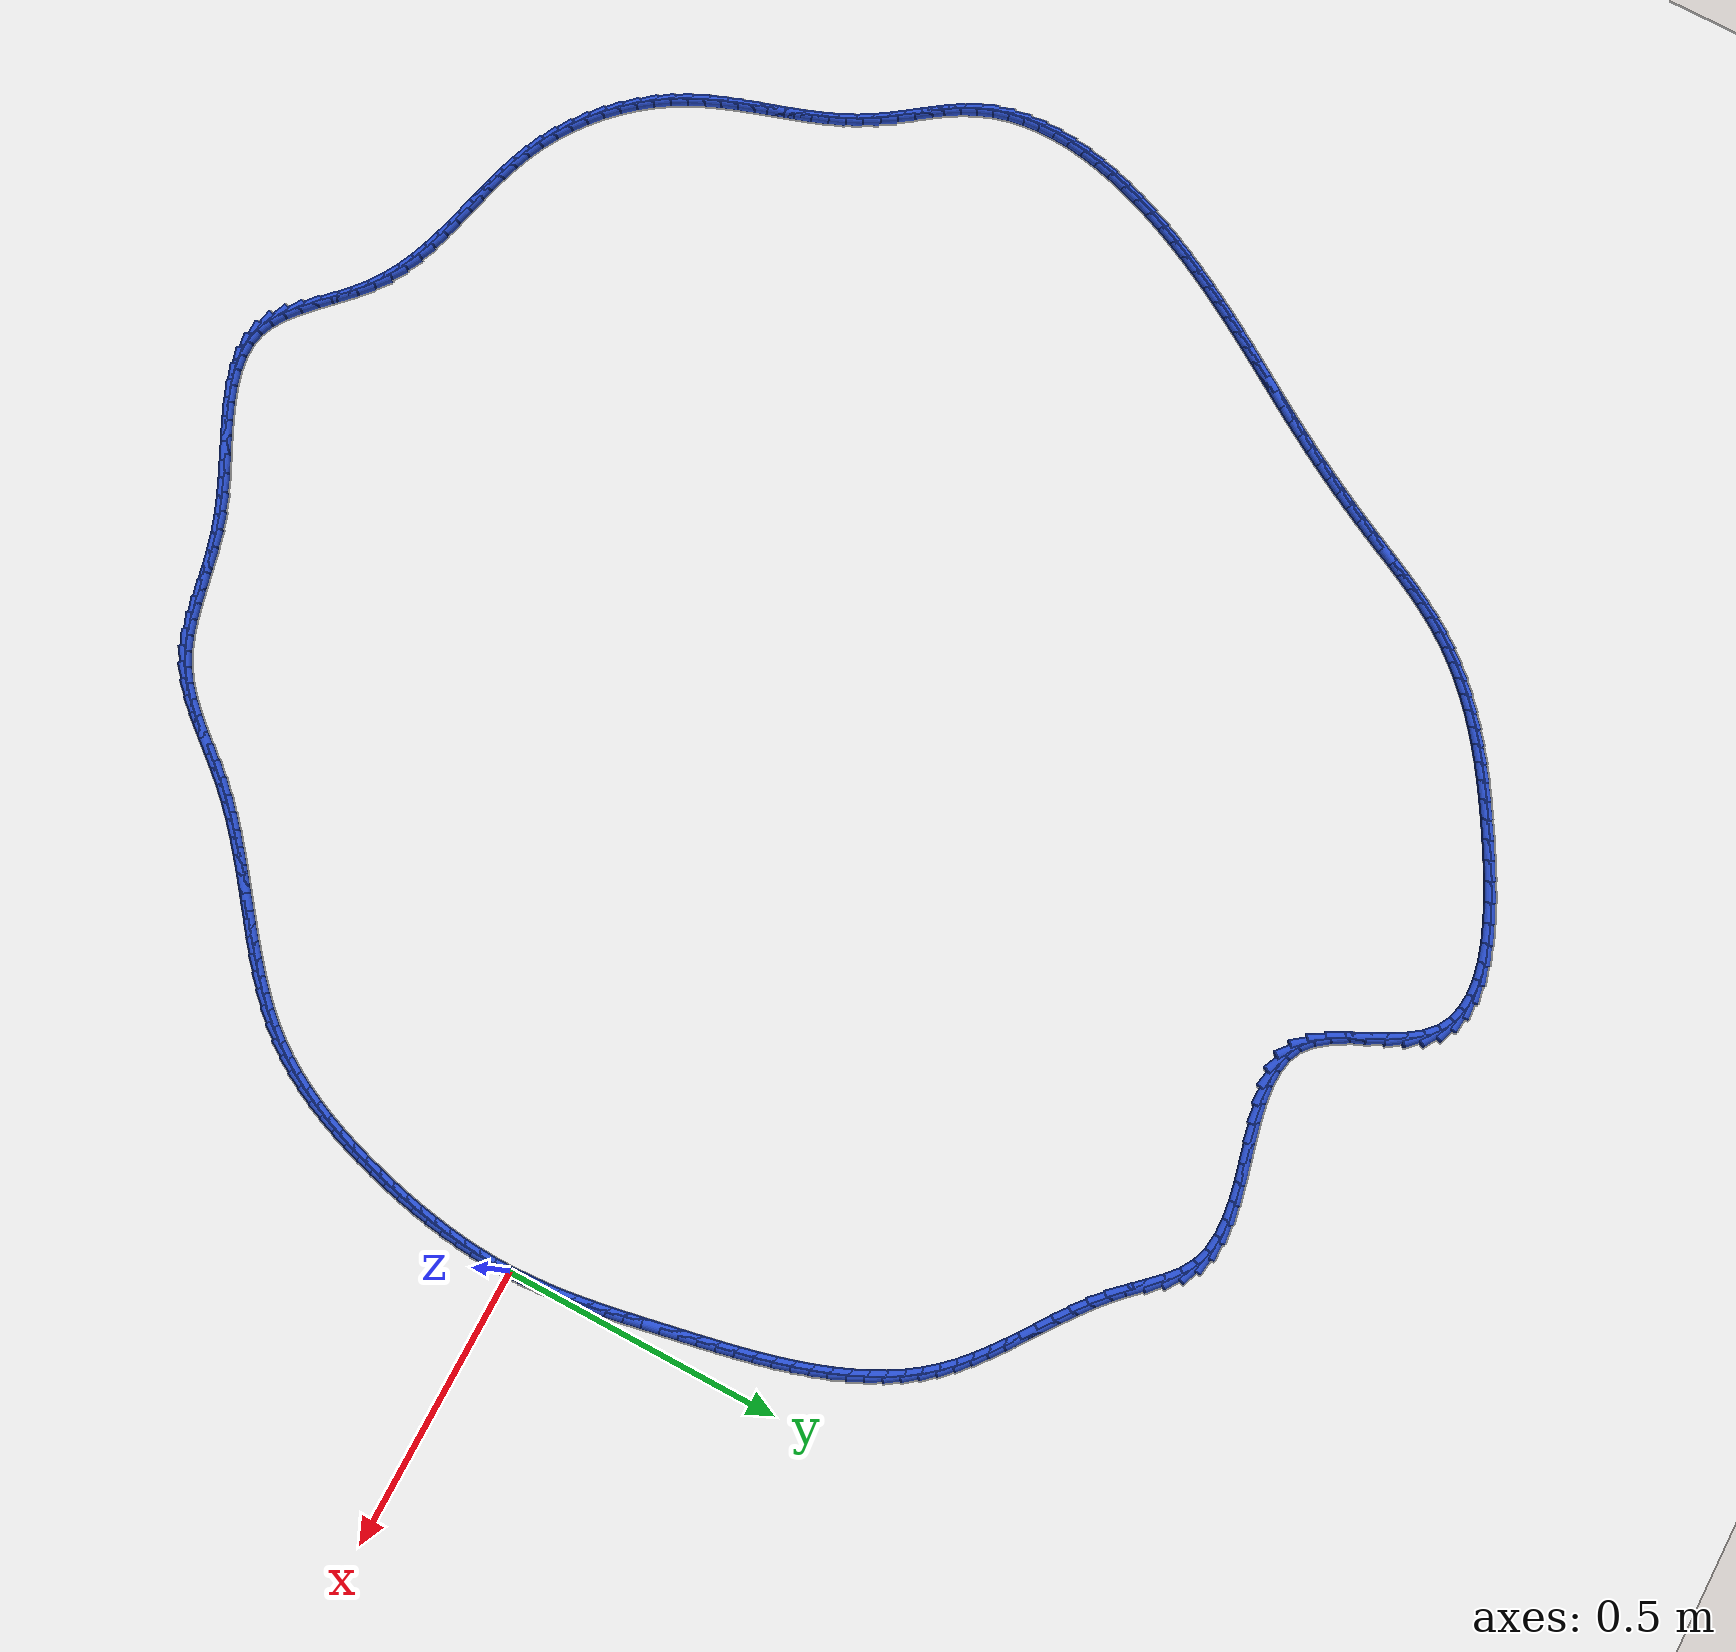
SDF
<sdf version="1.6">
 <world name="default">
  <light name="sun" type="directional">
   <pose>0 0 10 0 -0 0</pose>
   <diffuse>0.8 0.8 0.8 1</diffuse>
   <specular>0.2 0.2 0.2 1</specular>
   <attenuation>
    <range>1000</range>
    <constant>0.9</constant>
    <linear>0.01</linear>
    <quadratic>0.001</quadratic>
   </attenuation>
   <direction>-0.5 0.1 -0.9</direction>
  </light>
  <model name="ground_plane">
   <static>1</static>
   <link name="link">
    <collision name="collision">
     <geometry><plane><normal>0 0 1</normal><size>100 100</size></plane></geometry>
     <surface><friction><ode><mu>100</mu><mu2>50</mu2></ode></friction></surface>
    </collision>
    <visual name="visual">
     <cast_shadows>0</cast_shadows>
     <geometry><plane><normal>0 0 1</normal><size>100 100</size></plane></geometry>
     <material>
      <script><uri>file://media/materials/scripts/gazebo.material</uri><name>Gazebo/WhiteGlow</name></script>
     </material>
    </visual>
   </link>
  </model>
  <gravity>0 0 -9.8</gravity>
  <magnetic_field>6e-06 2.3e-05 -4.2e-05</magnetic_field>
  <atmosphere type="adiabatic"/>
  <physics name="default_physics" default="0" type="ode">
   <max_step_size>0.001</max_step_size>
   <real_time_factor>1</real_time_factor>
   <real_time_update_rate>1000</real_time_update_rate>
  </physics>
  <scene><ambient>0.4 0.4 0.4 1</ambient><background>0.7 0.7 0.7 1</background><shadows>1</shadows></scene>
  <spherical_coordinates>
   <surface_model>EARTH_WGS84</surface_model>
   <latitude_deg>0</latitude_deg>
   <longitude_deg>0</longitude_deg>
   <elevation>0</elevation>
   <heading_deg>0</heading_deg>
  </spherical_coordinates>
  <model name="line">
   <link name="link_0">
    <pose>8.673617379884035e-18 6.938893903907228e-17 0.01 0 1.57 -1.534834732647551</pose>
    <collision name="collision">
     <geometry><cylinder><radius>0.01</radius><length>0.08</length></cylinder></geometry>
    </collision>
    <visual name="visual">
     <material>
      <script><name>Gazebo/Blue</name><uri>file://media/materials/scripts/gazebo.material</uri></script>
     </material>
     <geometry><cylinder><radius>0.01</radius><length>0.08</length></cylinder></geometry>
    </visual>
   </link>
   <link name="link_1">
    <pose>-0.001085270482683053 0.030165587233258163 0.01 0 1.57 -1.4984836230928305</pose>
    <collision name="collision">
     <geometry><cylinder><radius>0.01</radius><length>0.08</length></cylinder></geometry>
    </collision>
    <visual name="visual">
     <material>
      <script><name>Gazebo/Blue</name><uri>file://media/materials/scripts/gazebo.material</uri></script>
     </material>
     <geometry><cylinder><radius>0.01</radius><length>0.08</length></cylinder></geometry>
    </visual>
   </link>
   <link name="link_2">
    <pose>-0.003266642161739448 0.060278804111640286 0.01 0 1.57 -1.4668365130238021</pose>
    <collision name="collision">
     <geometry><cylinder><radius>0.01</radius><length>0.08</length></cylinder></geometry>
    </collision>
    <visual name="visual">
     <material>
      <script><name>Gazebo/Blue</name><uri>file://media/materials/scripts/gazebo.material</uri></script>
     </material>
     <geometry><cylinder><radius>0.01</radius><length>0.08</length></cylinder></geometry>
    </visual>
   </link>
   <link name="link_3">
    <pose>-0.006407655895817889 0.0903836091083243 0.01 0 1.57 -1.4400223874380829</pose>
    <collision name="collision">
     <geometry><cylinder><radius>0.01</radius><length>0.08</length></cylinder></geometry>
    </collision>
    <visual name="visual">
     <material>
      <script><name>Gazebo/Blue</name><uri>file://media/materials/scripts/gazebo.material</uri></script>
     </material>
     <geometry><cylinder><radius>0.01</radius><length>0.08</length></cylinder></geometry>
    </visual>
   </link>
   <link name="link_4">
    <pose>-0.010371852543567074 0.12052396069648796 0.01 0 1.57 -1.4180916667990704</pose>
    <collision name="collision">
     <geometry><cylinder><radius>0.01</radius><length>0.08</length></cylinder></geometry>
    </collision>
    <visual name="visual">
     <material>
      <script><name>Gazebo/Blue</name><uri>file://media/materials/scripts/gazebo.material</uri></script>
     </material>
     <geometry><cylinder><radius>0.01</radius><length>0.08</length></cylinder></geometry>
    </visual>
   </link>
   <link name="link_5">
    <pose>-0.015022772963635717 0.15074381734930922 0.01 0 1.57 -1.4010349243635654</pose>
    <collision name="collision">
     <geometry><cylinder><radius>0.01</radius><length>0.08</length></cylinder></geometry>
    </collision>
    <visual name="visual">
     <material>
      <script><name>Gazebo/Blue</name><uri>file://media/materials/scripts/gazebo.material</uri></script>
     </material>
     <geometry><cylinder><radius>0.01</radius><length>0.08</length></cylinder></geometry>
    </visual>
   </link>
   <link name="link_6">
    <pose>-0.02022395801467251 0.18108713753996575 0.01 0 1.57 -1.388799495935072</pose>
    <collision name="collision">
     <geometry><cylinder><radius>0.01</radius><length>0.08</length></cylinder></geometry>
    </collision>
    <visual name="visual">
     <material>
      <script><name>Gazebo/Blue</name><uri>file://media/materials/scripts/gazebo.material</uri></script>
     </material>
     <geometry><cylinder><radius>0.01</radius><length>0.08</length></cylinder></geometry>
    </visual>
   </link>
   <link name="link_7">
    <pose>-0.025838948555326157 0.2115978797416354 0.01 0 1.57 -1.3813028904055904</pose>
    <collision name="collision">
     <geometry><cylinder><radius>0.01</radius><length>0.08</length></cylinder></geometry>
    </collision>
    <visual name="visual">
     <material>
      <script><name>Gazebo/Blue</name><uri>file://media/materials/scripts/gazebo.material</uri></script>
     </material>
     <geometry><cylinder><radius>0.01</radius><length>0.08</length></cylinder></geometry>
    </visual>
   </link>
   <link name="link_8">
    <pose>-0.03173128544424536 0.24232000242749607 0.01 0 1.57 -1.37844051123567</pose>
    <collision name="collision">
     <geometry><cylinder><radius>0.01</radius><length>0.08</length></cylinder></geometry>
    </collision>
    <visual name="visual">
     <material>
      <script><name>Gazebo/Blue</name><uri>file://media/materials/scripts/gazebo.material</uri></script>
     </material>
     <geometry><cylinder><radius>0.01</radius><length>0.08</length></cylinder></geometry>
    </visual>
   </link>
   <link name="link_9">
    <pose>-0.037764569140190045 0.2732974254342189 0.01 0 1.57 -1.3781064089530728</pose>
    <collision name="collision">
     <geometry><cylinder><radius>0.01</radius><length>0.08</length></cylinder></geometry>
    </collision>
    <visual name="visual">
     <material>
      <script><name>Gazebo/Blue</name><uri>file://media/materials/scripts/gazebo.material</uri></script>
     </material>
     <geometry><cylinder><radius>0.01</radius><length>0.08</length></cylinder></geometry>
    </visual>
   </link>
   <link name="link_10">
    <pose>-0.043859726055517766 0.3045369063425117 0.01 0 1.57 -1.3745708825909058</pose>
    <collision name="collision">
     <geometry><cylinder><radius>0.01</radius><length>0.08</length></cylinder></geometry>
    </collision>
    <visual name="visual">
     <material>
      <script><name>Gazebo/Blue</name><uri>file://media/materials/scripts/gazebo.material</uri></script>
     </material>
     <geometry><cylinder><radius>0.01</radius><length>0.08</length></cylinder></geometry>
    </visual>
   </link>
   <link name="link_11">
    <pose>-0.050101890725530895 0.33593875279351376 0.01 0 1.57 -1.3668533356605939</pose>
    <collision name="collision">
     <geometry><cylinder><radius>0.01</radius><length>0.08</length></cylinder></geometry>
    </collision>
    <visual name="visual">
     <material>
      <script><name>Gazebo/Blue</name><uri>file://media/materials/scripts/gazebo.material</uri></script>
     </material>
     <geometry><cylinder><radius>0.01</radius><length>0.08</length></cylinder></geometry>
    </visual>
   </link>
   <link name="link_12">
    <pose>-0.05660541382023284 0.36738433270895526 0.01 0 1.57 -1.3549246989037658</pose>
    <collision name="collision">
     <geometry><cylinder><radius>0.01</radius><length>0.08</length></cylinder></geometry>
    </collision>
    <visual name="visual">
     <material>
      <script><name>Gazebo/Blue</name><uri>file://media/materials/scripts/gazebo.material</uri></script>
     </material>
     <geometry><cylinder><radius>0.01</radius><length>0.08</length></cylinder></geometry>
    </visual>
   </link>
   <link name="link_13">
    <pose>-0.06348464600962694 0.398755014010566 0.01 0 1.57 -1.3386880151742515</pose>
    <collision name="collision">
     <geometry><cylinder><radius>0.01</radius><length>0.08</length></cylinder></geometry>
    </collision>
    <visual name="visual">
     <material>
      <script><name>Gazebo/Blue</name><uri>file://media/materials/scripts/gazebo.material</uri></script>
     </material>
     <geometry><cylinder><radius>0.01</radius><length>0.08</length></cylinder></geometry>
    </visual>
   </link>
   <link name="link_14">
    <pose>-0.07085393796371661 0.42993216462007633 0.01 0 1.57 -1.317982526979555</pose>
    <collision name="collision">
     <geometry><cylinder><radius>0.01</radius><length>0.08</length></cylinder></geometry>
    </collision>
    <visual name="visual">
     <material>
      <script><name>Gazebo/Blue</name><uri>file://media/materials/scripts/gazebo.material</uri></script>
     </material>
     <geometry><cylinder><radius>0.01</radius><length>0.08</length></cylinder></geometry>
    </visual>
   </link>
   <link name="link_15">
    <pose>-0.07882764035250522 0.460797152459216 0.01 0 1.57 -1.2925884182194418</pose>
    <collision name="collision">
     <geometry><cylinder><radius>0.01</radius><length>0.08</length></cylinder></geometry>
    </collision>
    <visual name="visual">
     <material>
      <script><name>Gazebo/Blue</name><uri>file://media/materials/scripts/gazebo.material</uri></script>
     </material>
     <geometry><cylinder><radius>0.01</radius><length>0.08</length></cylinder></geometry>
    </visual>
   </link>
   <link name="link_16">
    <pose>-0.08752010384599618 0.49123134544971525 0.01 0 1.57 -1.2622335733288337</pose>
    <collision name="collision">
     <geometry><cylinder><radius>0.01</radius><length>0.08</length></cylinder></geometry>
    </collision>
    <visual name="visual">
     <material>
      <script><name>Gazebo/Blue</name><uri>file://media/materials/scripts/gazebo.material</uri></script>
     </material>
     <geometry><cylinder><radius>0.01</radius><length>0.08</length></cylinder></geometry>
    </visual>
   </link>
   <link name="link_17">
    <pose>-0.0970456791141928 0.5211161115133038 0.01 0 1.57 -1.2266042166525681</pose>
    <collision name="collision">
     <geometry><cylinder><radius>0.01</radius><length>0.08</length></cylinder></geometry>
    </collision>
    <visual name="visual">
     <material>
      <script><name>Gazebo/Blue</name><uri>file://media/materials/scripts/gazebo.material</uri></script>
     </material>
     <geometry><cylinder><radius>0.01</radius><length>0.08</length></cylinder></geometry>
    </visual>
   </link>
   <link name="link_18">
    <pose>-0.10751871682709854 0.5503328185717121 0.01 0 1.57 -1.1853618739446046</pose>
    <collision name="collision">
     <geometry><cylinder><radius>0.01</radius><length>0.08</length></cylinder></geometry>
    </collision>
    <visual name="visual">
     <material>
      <script><name>Gazebo/Blue</name><uri>file://media/materials/scripts/gazebo.material</uri></script>
     </material>
     <geometry><cylinder><radius>0.01</radius><length>0.08</length></cylinder></geometry>
    </visual>
   </link>
   <link name="link_19">
    <pose>-0.11905356765471667 0.5787628345466697 0.01 0 1.57 -1.138169624929014</pose>
    <collision name="collision">
     <geometry><cylinder><radius>0.01</radius><length>0.08</length></cylinder></geometry>
    </collision>
    <visual name="visual">
     <material>
      <script><name>Gazebo/Blue</name><uri>file://media/materials/scripts/gazebo.material</uri></script>
     </material>
     <geometry><cylinder><radius>0.01</radius><length>0.08</length></cylinder></geometry>
    </visual>
   </link>
   <link name="link_20">
    <pose>-0.1317645822670507 0.606287527359907 0.01 0 1.57 -1.0847307844574157</pose>
    <collision name="collision">
     <geometry><cylinder><radius>0.01</radius><length>0.08</length></cylinder></geometry>
    </collision>
    <visual name="visual">
     <material>
      <script><name>Gazebo/Blue</name><uri>file://media/materials/scripts/gazebo.material</uri></script>
     </material>
     <geometry><cylinder><radius>0.01</radius><length>0.08</length></cylinder></geometry>
    </visual>
   </link>
   <link name="link_21">
    <pose>-0.14576611133410394 0.632788264933154 0.01 0 1.57 -1.0248424020184124</pose>
    <collision name="collision">
     <geometry><cylinder><radius>0.01</radius><length>0.08</length></cylinder></geometry>
    </collision>
    <visual name="visual">
     <material>
      <script><name>Gazebo/Blue</name><uri>file://media/materials/scripts/gazebo.material</uri></script>
     </material>
     <geometry><cylinder><radius>0.01</radius><length>0.08</length></cylinder></geometry>
    </visual>
   </link>
   <link name="link_22">
    <pose>-0.16117250552587983 0.6581464151881405 0.01 0 1.57 -0.9584635029178982</pose>
    <collision name="collision">
     <geometry><cylinder><radius>0.01</radius><length>0.08</length></cylinder></geometry>
    </collision>
    <visual name="visual">
     <material>
      <script><name>Gazebo/Blue</name><uri>file://media/materials/scripts/gazebo.material</uri></script>
     </material>
     <geometry><cylinder><radius>0.01</radius><length>0.08</length></cylinder></geometry>
    </visual>
   </link>
   <link name="link_23">
    <pose>-0.17809811551238164 0.6822433460465965 0.01 0 1.57 -0.8857930297932988</pose>
    <collision name="collision">
     <geometry><cylinder><radius>0.01</radius><length>0.08</length></cylinder></geometry>
    </collision>
    <visual name="visual">
     <material>
      <script><name>Gazebo/Blue</name><uri>file://media/materials/scripts/gazebo.material</uri></script>
     </material>
     <geometry><cylinder><radius>0.01</radius><length>0.08</length></cylinder></geometry>
    </visual>
   </link>
   <link name="link_24">
    <pose>-0.1966572919636128 0.7049604254302522 0.01 0 1.57 -0.8095331828342889</pose>
    <collision name="collision">
     <geometry><cylinder><radius>0.01</radius><length>0.08</length></cylinder></geometry>
    </collision>
    <visual name="visual">
     <material>
      <script><name>Gazebo/Blue</name><uri>file://media/materials/scripts/gazebo.material</uri></script>
     </material>
     <geometry><cylinder><radius>0.01</radius><length>0.08</length></cylinder></geometry>
    </visual>
   </link>
   <link name="link_25">
    <pose>-0.21692015393489472 0.7262257660330504 0.01 0 1.57 -0.743160662270411</pose>
    <collision name="collision">
     <geometry><cylinder><radius>0.01</radius><length>0.08</length></cylinder></geometry>
    </collision>
    <visual name="visual">
     <material>
      <script><name>Gazebo/Blue</name><uri>file://media/materials/scripts/gazebo.material</uri></script>
     </material>
     <geometry><cylinder><radius>0.01</radius><length>0.08</length></cylinder></geometry>
    </visual>
   </link>
   <link name="link_26">
    <pose>-0.23869978740385892 0.7462391177648506 0.01 0 1.57 -0.6916082637496144</pose>
    <collision name="collision">
     <geometry><cylinder><radius>0.01</radius><length>0.08</length></cylinder></geometry>
    </collision>
    <visual name="visual">
     <material>
      <script><name>Gazebo/Blue</name><uri>file://media/materials/scripts/gazebo.material</uri></script>
     </material>
     <geometry><cylinder><radius>0.01</radius><length>0.08</length></cylinder></geometry>
    </visual>
   </link>
   <link name="link_27">
    <pose>-0.2617166717778914 0.7652980988376912 0.01 0 1.57 -0.6546581979336694</pose>
    <collision name="collision">
     <geometry><cylinder><radius>0.01</radius><length>0.08</length></cylinder></geometry>
    </collision>
    <visual name="visual">
     <material>
      <script><name>Gazebo/Blue</name><uri>file://media/materials/scripts/gazebo.material</uri></script>
     </material>
     <geometry><cylinder><radius>0.01</radius><length>0.08</length></cylinder></geometry>
    </visual>
   </link>
   <link name="link_28">
    <pose>-0.2856911630514536 0.7837004578886254 0.01 0 1.57 -0.6318254795962253</pose>
    <collision name="collision">
     <geometry><cylinder><radius>0.01</radius><length>0.08</length></cylinder></geometry>
    </collision>
    <visual name="visual">
     <material>
      <script><name>Gazebo/Blue</name><uri>file://media/materials/scripts/gazebo.material</uri></script>
     </material>
     <geometry><cylinder><radius>0.01</radius><length>0.08</length></cylinder></geometry>
    </visual>
   </link>
   <link name="link_29">
    <pose>-0.31034361721900694 0.8017439435547072 0.01 0 1.57 -0.6225967794546875</pose>
    <collision name="collision">
     <geometry><cylinder><radius>0.01</radius><length>0.08</length></cylinder></geometry>
    </collision>
    <visual name="visual">
     <material>
      <script><name>Gazebo/Blue</name><uri>file://media/materials/scripts/gazebo.material</uri></script>
     </material>
     <geometry><cylinder><radius>0.01</radius><length>0.08</length></cylinder></geometry>
    </visual>
   </link>
   <link name="link_30">
    <pose>-0.33539439027501317 0.819726304472991 0.01 0 1.57 -0.6265560743086076</pose>
    <collision name="collision">
     <geometry><cylinder><radius>0.01</radius><length>0.08</length></cylinder></geometry>
    </collision>
    <visual name="visual">
     <material>
      <script><name>Gazebo/Blue</name><uri>file://media/materials/scripts/gazebo.material</uri></script>
     </material>
     <geometry><cylinder><radius>0.01</radius><length>0.08</length></cylinder></geometry>
    </visual>
   </link>
   <link name="link_31">
    <pose>-0.36056383821393345 0.8379452892805298 0.01 0 1.57 -0.6434242848944025</pose>
    <collision name="collision">
     <geometry><cylinder><radius>0.01</radius><length>0.08</length></cylinder></geometry>
    </collision>
    <visual name="visual">
     <material>
      <script><name>Gazebo/Blue</name><uri>file://media/materials/scripts/gazebo.material</uri></script>
     </material>
     <geometry><cylinder><radius>0.01</radius><length>0.08</length></cylinder></geometry>
    </visual>
   </link>
   <link name="link_32">
    <pose>-0.38557231703022954 0.8566986466143776 0.01 0 1.57 -0.6730306936593158</pose>
    <collision name="collision">
     <geometry><cylinder><radius>0.01</radius><length>0.08</length></cylinder></geometry>
    </collision>
    <visual name="visual">
     <material>
      <script><name>Gazebo/Blue</name><uri>file://media/materials/scripts/gazebo.material</uri></script>
     </material>
     <geometry><cylinder><radius>0.01</radius><length>0.08</length></cylinder></geometry>
    </visual>
   </link>
   <link name="link_33">
    <pose>-0.4101401827183626 0.8762841251115882 0.01 0 1.57 -0.715225144321009</pose>
    <collision name="collision">
     <geometry><cylinder><radius>0.01</radius><length>0.08</length></cylinder></geometry>
    </collision>
    <visual name="visual">
     <material>
      <script><name>Gazebo/Blue</name><uri>file://media/materials/scripts/gazebo.material</uri></script>
     </material>
     <geometry><cylinder><radius>0.01</radius><length>0.08</length></cylinder></geometry>
    </visual>
   </link>
   <link name="link_34">
    <pose>-0.4339877912727943 0.8969994734092154 0.01 0 1.57 -0.7697116626267009</pose>
    <collision name="collision">
     <geometry><cylinder><radius>0.01</radius><length>0.08</length></cylinder></geometry>
    </collision>
    <visual name="visual">
     <material>
      <script><name>Gazebo/Blue</name><uri>file://media/materials/scripts/gazebo.material</uri></script>
     </material>
     <geometry><cylinder><radius>0.01</radius><length>0.08</length></cylinder></geometry>
    </visual>
   </link>
   <link name="link_35">
    <pose>-0.45683587634639883 0.9191417591049718 0.01 0 1.57 -0.8173952106771679</pose>
    <collision name="collision">
     <geometry><cylinder><radius>0.01</radius><length>0.08</length></cylinder></geometry>
    </collision>
    <visual name="visual">
     <material>
      <script><name>Gazebo/Blue</name><uri>file://media/materials/scripts/gazebo.material</uri></script>
     </material>
     <geometry><cylinder><radius>0.01</radius><length>0.08</length></cylinder></geometry>
    </visual>
   </link>
   <link name="link_36">
    <pose>-0.4787085601250067 0.9424609428878555 0.01 0 1.57 -0.8065885261360701</pose>
    <collision name="collision">
     <geometry><cylinder><radius>0.01</radius><length>0.08</length></cylinder></geometry>
    </collision>
    <visual name="visual">
     <material>
      <script><name>Gazebo/Blue</name><uri>file://media/materials/scripts/gazebo.material</uri></script>
     </material>
     <geometry><cylinder><radius>0.01</radius><length>0.08</length></cylinder></geometry>
    </visual>
   </link>
   <link name="link_37">
    <pose>-0.5004796161615563 0.9651747913048776 0.01 0 1.57 -0.7239396289864225</pose>
    <collision name="collision">
     <geometry><cylinder><radius>0.01</radius><length>0.08</length></cylinder></geometry>
    </collision>
    <visual name="visual">
     <material>
      <script><name>Gazebo/Blue</name><uri>file://media/materials/scripts/gazebo.material</uri></script>
     </material>
     <geometry><cylinder><radius>0.01</radius><length>0.08</length></cylinder></geometry>
    </visual>
   </link>
   <link name="link_38">
    <pose>-0.5231704281639824 0.9852348824126399 0.01 0 1.57 -0.5575394265091913</pose>
    <collision name="collision">
     <geometry><cylinder><radius>0.01</radius><length>0.08</length></cylinder></geometry>
    </collision>
    <visual name="visual">
     <material>
      <script><name>Gazebo/Blue</name><uri>file://media/materials/scripts/gazebo.material</uri></script>
     </material>
     <geometry><cylinder><radius>0.01</radius><length>0.08</length></cylinder></geometry>
    </visual>
   </link>
   <link name="link_39">
    <pose>-0.5478020891732953 1.0005933897633656 0.01 0 1.57 -0.3286391392292028</pose>
    <collision name="collision">
     <geometry><cylinder><radius>0.01</radius><length>0.08</length></cylinder></geometry>
    </collision>
    <visual name="visual">
     <material>
      <script><name>Gazebo/Blue</name><uri>file://media/materials/scripts/gazebo.material</uri></script>
     </material>
     <geometry><cylinder><radius>0.01</radius><length>0.08</length></cylinder></geometry>
    </visual>
   </link>
   <link name="link_40">
    <pose>-0.5750607330315112 1.0098887250731357 0.01 0 1.57 -0.13031589210065933</pose>
    <collision name="collision">
     <geometry><cylinder><radius>0.01</radius><length>0.08</length></cylinder></geometry>
    </collision>
    <visual name="visual">
     <material>
      <script><name>Gazebo/Blue</name><uri>file://media/materials/scripts/gazebo.material</uri></script>
     </material>
     <geometry><cylinder><radius>0.01</radius><length>0.08</length></cylinder></geometry>
    </visual>
   </link>
   <link name="link_41">
    <pose>-0.6046525242370745 1.0137669844714943 0.01 0 1.57 0.016769471340675447</pose>
    <collision name="collision">
     <geometry><cylinder><radius>0.01</radius><length>0.08</length></cylinder></geometry>
    </collision>
    <visual name="visual">
     <material>
      <script><name>Gazebo/Blue</name><uri>file://media/materials/scripts/gazebo.material</uri></script>
     </material>
     <geometry><cylinder><radius>0.01</radius><length>0.08</length></cylinder></geometry>
    </visual>
   </link>
   <link name="link_42">
    <pose>-0.6361053583000896 1.0132394876244595 0.01 0 1.57 0.11885618852034543</pose>
    <collision name="collision">
     <geometry><cylinder><radius>0.01</radius><length>0.08</length></cylinder></geometry>
    </collision>
    <visual name="visual">
     <material>
      <script><name>Gazebo/Blue</name><uri>file://media/materials/scripts/gazebo.material</uri></script>
     </material>
     <geometry><cylinder><radius>0.01</radius><length>0.08</length></cylinder></geometry>
    </visual>
   </link>
   <link name="link_43">
    <pose>-0.6689471307306605 1.0093175541980492 0.01 0 1.57 0.18464137382621498</pose>
    <collision name="collision">
     <geometry><cylinder><radius>0.01</radius><length>0.08</length></cylinder></geometry>
    </collision>
    <visual name="visual">
     <material>
      <script><name>Gazebo/Blue</name><uri>file://media/materials/scripts/gazebo.material</uri></script>
     </material>
     <geometry><cylinder><radius>0.01</radius><length>0.08</length></cylinder></geometry>
    </visual>
   </link>
   <link name="link_44">
    <pose>-0.702705737038891 1.0030125038582813 0.01 0 1.57 0.22078834679530712</pose>
    <collision name="collision">
     <geometry><cylinder><radius>0.01</radius><length>0.08</length></cylinder></geometry>
    </collision>
    <visual name="visual">
     <material>
      <script><name>Gazebo/Blue</name><uri>file://media/materials/scripts/gazebo.material</uri></script>
     </material>
     <geometry><cylinder><radius>0.01</radius><length>0.08</length></cylinder></geometry>
    </visual>
   </link>
   <link name="link_45">
    <pose>-0.7369090727348862 0.995335656271175 0.01 0 1.57 0.23097761888623183</pose>
    <collision name="collision">
     <geometry><cylinder><radius>0.01</radius><length>0.08</length></cylinder></geometry>
    </collision>
    <visual name="visual">
     <material>
      <script><name>Gazebo/Blue</name><uri>file://media/materials/scripts/gazebo.material</uri></script>
     </material>
     <geometry><cylinder><radius>0.01</radius><length>0.08</length></cylinder></geometry>
    </visual>
   </link>
   <link name="link_46">
    <pose>-0.7710850333287492 0.9872983311027479 0.01 0 1.57 0.2159173933694123</pose>
    <collision name="collision">
     <geometry><cylinder><radius>0.01</radius><length>0.08</length></cylinder></geometry>
    </collision>
    <visual name="visual">
     <material>
      <script><name>Gazebo/Blue</name><uri>file://media/materials/scripts/gazebo.material</uri></script>
     </material>
     <geometry><cylinder><radius>0.01</radius><length>0.08</length></cylinder></geometry>
    </visual>
   </link>
   <link name="link_47">
    <pose>-0.8047615143305851 0.9799118480190182 0.01 0 1.57 0.1732742771846421</pose>
    <collision name="collision">
     <geometry><cylinder><radius>0.01</radius><length>0.08</length></cylinder></geometry>
    </collision>
    <visual name="visual">
     <material>
      <script><name>Gazebo/Blue</name><uri>file://media/materials/scripts/gazebo.material</uri></script>
     </material>
     <geometry><cylinder><radius>0.01</radius><length>0.08</length></cylinder></geometry>
    </visual>
   </link>
   <link name="link_48">
    <pose>-0.8374664112504975 0.974187526686004 0.01 0 1.57 0.09728380554751538</pose>
    <collision name="collision">
     <geometry><cylinder><radius>0.01</radius><length>0.08</length></cylinder></geometry>
    </collision>
    <visual name="visual">
     <material>
      <script><name>Gazebo/Blue</name><uri>file://media/materials/scripts/gazebo.material</uri></script>
     </material>
     <geometry><cylinder><radius>0.01</radius><length>0.08</length></cylinder></geometry>
    </visual>
   </link>
   <link name="link_49">
    <pose>-0.8687276195985902 0.9711366867697233 0.01 0 1.57 -0.02160005449167211</pose>
    <collision name="collision">
     <geometry><cylinder><radius>0.01</radius><length>0.08</length></cylinder></geometry>
    </collision>
    <visual name="visual">
     <material>
      <script><name>Gazebo/Blue</name><uri>file://media/materials/scripts/gazebo.material</uri></script>
     </material>
     <geometry><cylinder><radius>0.01</radius><length>0.08</length></cylinder></geometry>
    </visual>
   </link>
   <link name="link_50">
    <pose>-0.8980730348849685 0.9717706479361947 0.01 0 1.57 -0.19520377586221402</pose>
    <collision name="collision">
     <geometry><cylinder><radius>0.01</radius><length>0.08</length></cylinder></geometry>
    </collision>
    <visual name="visual">
     <material>
      <script><name>Gazebo/Blue</name><uri>file://media/materials/scripts/gazebo.material</uri></script>
     </material>
     <geometry><cylinder><radius>0.01</radius><length>0.08</length></cylinder></geometry>
    </visual>
   </link>
   <link name="link_51">
    <pose>-0.9250305526197355 0.977100729851436 0.01 0 1.57 -0.42951628276426856</pose>
    <collision name="collision">
     <geometry><cylinder><radius>0.01</radius><length>0.08</length></cylinder></geometry>
    </collision>
    <visual name="visual">
     <material>
      <script><name>Gazebo/Blue</name><uri>file://media/materials/scripts/gazebo.material</uri></script>
     </material>
     <geometry><cylinder><radius>0.01</radius><length>0.08</length></cylinder></geometry>
    </visual>
   </link>
   <link name="link_52">
    <pose>-0.9491280683129961 0.9881382521814659 0.01 0 1.57 -0.7008071572866809</pose>
    <collision name="collision">
     <geometry><cylinder><radius>0.01</radius><length>0.08</length></cylinder></geometry>
    </collision>
    <visual name="visual">
     <material>
      <script><name>Gazebo/Blue</name><uri>file://media/materials/scripts/gazebo.material</uri></script>
     </material>
     <geometry><cylinder><radius>0.01</radius><length>0.08</length></cylinder></geometry>
    </visual>
   </link>
   <link name="link_53">
    <pose>-0.9699751602771564 1.005726299793805 0.01 0 1.57 -0.9122067546751638</pose>
    <collision name="collision">
     <geometry><cylinder><radius>0.01</radius><length>0.08</length></cylinder></geometry>
    </collision>
    <visual name="visual">
     <material>
      <script><name>Gazebo/Blue</name><uri>file://media/materials/scripts/gazebo.material</uri></script>
     </material>
     <geometry><cylinder><radius>0.01</radius><length>0.08</length></cylinder></geometry>
    </visual>
   </link>
   <link name="link_54">
    <pose>-0.9880009473295859 1.0290200229133375 0.01 0 1.57 -1.035854640714874</pose>
    <collision name="collision">
     <geometry><cylinder><radius>0.01</radius><length>0.08</length></cylinder></geometry>
    </collision>
    <visual name="visual">
     <material>
      <script><name>Gazebo/Blue</name><uri>file://media/materials/scripts/gazebo.material</uri></script>
     </material>
     <geometry><cylinder><radius>0.01</radius><length>0.08</length></cylinder></geometry>
    </visual>
   </link>
   <link name="link_55">
    <pose>-1.0041074506242116 1.0562005769085399 0.01 0 1.57 -1.0941936350383803</pose>
    <collision name="collision">
     <geometry><cylinder><radius>0.01</radius><length>0.08</length></cylinder></geometry>
    </collision>
    <visual name="visual">
     <material>
      <script><name>Gazebo/Blue</name><uri>file://media/materials/scripts/gazebo.material</uri></script>
     </material>
     <geometry><cylinder><radius>0.01</radius><length>0.08</length></cylinder></geometry>
    </visual>
   </link>
   <link name="link_56">
    <pose>-1.0192024056913565 1.08543734775537 0.01 0 1.57 -1.1001150137602542</pose>
    <collision name="collision">
     <geometry><cylinder><radius>0.01</radius><length>0.08</length></cylinder></geometry>
    </collision>
    <visual name="visual">
     <material>
      <script><name>Gazebo/Blue</name><uri>file://media/materials/scripts/gazebo.material</uri></script>
     </material>
     <geometry><cylinder><radius>0.01</radius><length>0.08</length></cylinder></geometry>
    </visual>
   </link>
   <link name="link_57">
    <pose>-1.034193548061346 1.1148997214297889 0.01 0 1.57 -1.0549966539734452</pose>
    <collision name="collision">
     <geometry><cylinder><radius>0.01</radius><length>0.08</length></cylinder></geometry>
    </collision>
    <visual name="visual">
     <material>
      <script><name>Gazebo/Blue</name><uri>file://media/materials/scripts/gazebo.material</uri></script>
     </material>
     <geometry><cylinder><radius>0.01</radius><length>0.08</length></cylinder></geometry>
    </visual>
   </link>
   <link name="link_58">
    <pose>-1.0499886132645053 1.1427570839077557 0.01 0 1.57 -0.9488508935099754</pose>
    <collision name="collision">
     <geometry><cylinder><radius>0.01</radius><length>0.08</length></cylinder></geometry>
    </collision>
    <visual name="visual">
     <material>
      <script><name>Gazebo/Blue</name><uri>file://media/materials/scripts/gazebo.material</uri></script>
     </material>
     <geometry><cylinder><radius>0.01</radius><length>0.08</length></cylinder></geometry>
    </visual>
   </link>
   <link name="link_59">
    <pose>-1.0674953368311586 1.1671788211652299 0.01 0 1.57 -0.7615122972132938</pose>
    <collision name="collision">
     <geometry><cylinder><radius>0.01</radius><length>0.08</length></cylinder></geometry>
    </collision>
    <visual name="visual">
     <material>
      <script><name>Gazebo/Blue</name><uri>file://media/materials/scripts/gazebo.material</uri></script>
     </material>
     <geometry><cylinder><radius>0.01</radius><length>0.08</length></cylinder></geometry>
    </visual>
   </link>
   <link name="link_60">
    <pose>-1.0876102283318687 1.1863550321269283 0.01 0 1.57 -0.5149608002329189</pose>
    <collision name="collision">
     <geometry><cylinder><radius>0.01</radius><length>0.08</length></cylinder></geometry>
    </collision>
    <visual name="visual">
     <material>
      <script><name>Gazebo/Blue</name><uri>file://media/materials/scripts/gazebo.material</uri></script>
     </material>
     <geometry><cylinder><radius>0.01</radius><length>0.08</length></cylinder></geometry>
    </visual>
   </link>
   <link name="link_61">
    <pose>-1.1107132901004675 1.1994288200178327 0.01 0 1.57 -0.28146919483834854</pose>
    <collision name="collision">
     <geometry><cylinder><radius>0.01</radius><length>0.08</length></cylinder></geometry>
    </collision>
    <visual name="visual">
     <material>
      <script><name>Gazebo/Blue</name><uri>file://media/materials/scripts/gazebo.material</uri></script>
     </material>
     <geometry><cylinder><radius>0.01</radius><length>0.08</length></cylinder></geometry>
    </visual>
   </link>
   <link name="link_62">
    <pose>-1.1364631551109985 1.2068742821963363 0.01 0 1.57 -0.08515277672372246</pose>
    <collision name="collision">
     <geometry><cylinder><radius>0.01</radius><length>0.08</length></cylinder></geometry>
    </collision>
    <visual name="visual">
     <material>
      <script><name>Gazebo/Blue</name><uri>file://media/materials/scripts/gazebo.material</uri></script>
     </material>
     <geometry><cylinder><radius>0.01</radius><length>0.08</length></cylinder></geometry>
    </visual>
   </link>
   <link name="link_63">
    <pose>-1.1644648192111728 1.2092644815500935 0.01 0 1.57 0.06994960627136804</pose>
    <collision name="collision">
     <geometry><cylinder><radius>0.01</radius><length>0.08</length></cylinder></geometry>
    </collision>
    <visual name="visual">
     <material>
      <script><name>Gazebo/Blue</name><uri>file://media/materials/scripts/gazebo.material</uri></script>
     </material>
     <geometry><cylinder><radius>0.01</radius><length>0.08</length></cylinder></geometry>
    </visual>
   </link>
   <link name="link_64">
    <pose>-1.1943232782487003 1.207172480966758 0.01 0 1.57 0.18931121959816494</pose>
    <collision name="collision">
     <geometry><cylinder><radius>0.01</radius><length>0.08</length></cylinder></geometry>
    </collision>
    <visual name="visual">
     <material>
      <script><name>Gazebo/Blue</name><uri>file://media/materials/scripts/gazebo.material</uri></script>
     </material>
     <geometry><cylinder><radius>0.01</radius><length>0.08</length></cylinder></geometry>
    </visual>
   </link>
   <link name="link_65">
    <pose>-1.2256435280712912 1.2011713433339852 0.01 0 1.57 0.28068942077641557</pose>
    <collision name="collision">
     <geometry><cylinder><radius>0.01</radius><length>0.08</length></cylinder></geometry>
    </collision>
    <visual name="visual">
     <material>
      <script><name>Gazebo/Blue</name><uri>file://media/materials/scripts/gazebo.material</uri></script>
     </material>
     <geometry><cylinder><radius>0.01</radius><length>0.08</length></cylinder></geometry>
    </visual>
   </link>
   <link name="link_66">
    <pose>-1.258030564526657 1.1918341315394287 0.01 0 1.57 0.3508755567940025</pose>
    <collision name="collision">
     <geometry><cylinder><radius>0.01</radius><length>0.08</length></cylinder></geometry>
    </collision>
    <visual name="visual">
     <material>
      <script><name>Gazebo/Blue</name><uri>file://media/materials/scripts/gazebo.material</uri></script>
     </material>
     <geometry><cylinder><radius>0.01</radius><length>0.08</length></cylinder></geometry>
    </visual>
   </link>
   <link name="link_67">
    <pose>-1.2910893834625061 1.1797339084707434 0.01 0 1.57 0.4049801521559771</pose>
    <collision name="collision">
     <geometry><cylinder><radius>0.01</radius><length>0.08</length></cylinder></geometry>
    </collision>
    <visual name="visual">
     <material>
      <script><name>Gazebo/Blue</name><uri>file://media/materials/scripts/gazebo.material</uri></script>
     </material>
     <geometry><cylinder><radius>0.01</radius><length>0.08</length></cylinder></geometry>
    </visual>
   </link>
   <link name="link_68">
    <pose>-1.3244249807265502 1.1654437370155832 0.01 0 1.57 0.44660739720744025</pose>
    <collision name="collision">
     <geometry><cylinder><radius>0.01</radius><length>0.08</length></cylinder></geometry>
    </collision>
    <visual name="visual">
     <material>
      <script><name>Gazebo/Blue</name><uri>file://media/materials/scripts/gazebo.material</uri></script>
     </material>
     <geometry><cylinder><radius>0.01</radius><length>0.08</length></cylinder></geometry>
    </visual>
   </link>
   <link name="link_69">
    <pose>-1.357642352166499 1.1495366800616034 0.01 0 1.57 0.47818798590809763</pose>
    <collision name="collision">
     <geometry><cylinder><radius>0.01</radius><length>0.08</length></cylinder></geometry>
    </collision>
    <visual name="visual">
     <material>
      <script><name>Gazebo/Blue</name><uri>file://media/materials/scripts/gazebo.material</uri></script>
     </material>
     <geometry><cylinder><radius>0.01</radius><length>0.08</length></cylinder></geometry>
    </visual>
   </link>
   <link name="link_70">
    <pose>-1.3903464936300638 1.1325858004964573 0.01 0 1.57 0.5012455021325636</pose>
    <collision name="collision">
     <geometry><cylinder><radius>0.01</radius><length>0.08</length></cylinder></geometry>
    </collision>
    <visual name="visual">
     <material>
      <script><name>Gazebo/Blue</name><uri>file://media/materials/scripts/gazebo.material</uri></script>
     </material>
     <geometry><cylinder><radius>0.01</radius><length>0.08</length></cylinder></geometry>
    </visual>
   </link>
   <link name="link_71">
    <pose>-1.422142400964953 1.1151641612077998 0.01 0 1.57 0.5183120464710429</pose>
    <collision name="collision">
     <geometry><cylinder><radius>0.01</radius><length>0.08</length></cylinder></geometry>
    </collision>
    <visual name="visual">
     <material>
      <script><name>Gazebo/Blue</name><uri>file://media/materials/scripts/gazebo.material</uri></script>
     </material>
     <geometry><cylinder><radius>0.01</radius><length>0.08</length></cylinder></geometry>
    </visual>
   </link>
   <link name="link_72">
    <pose>-1.4527030272311239 1.0977347428777775 0.01 0 1.57 0.536891195430585</pose>
    <collision name="collision">
     <geometry><cylinder><radius>0.01</radius><length>0.08</length></cylinder></geometry>
    </collision>
    <visual name="visual">
     <material>
      <script><name>Gazebo/Blue</name><uri>file://media/materials/scripts/gazebo.material</uri></script>
     </material>
     <geometry><cylinder><radius>0.01</radius><length>0.08</length></cylinder></geometry>
    </visual>
   </link>
   <link name="link_73">
    <pose>-1.4819803511709255 1.0803085393942546 0.01 0 1.57 0.5590350211923778</pose>
    <collision name="collision">
     <geometry><cylinder><radius>0.01</radius><length>0.08</length></cylinder></geometry>
    </collision>
    <visual name="visual">
     <material>
      <script><name>Gazebo/Blue</name><uri>file://media/materials/scripts/gazebo.material</uri></script>
     </material>
     <geometry><cylinder><radius>0.01</radius><length>0.08</length></cylinder></geometry>
    </visual>
   </link>
   <link name="link_74">
    <pose>-1.5099979545357263 1.0627805567036637 0.01 0 1.57 0.5849057392485509</pose>
    <collision name="collision">
     <geometry><cylinder><radius>0.01</radius><length>0.08</length></cylinder></geometry>
    </collision>
    <visual name="visual">
     <material>
      <script><name>Gazebo/Blue</name><uri>file://media/materials/scripts/gazebo.material</uri></script>
     </material>
     <geometry><cylinder><radius>0.01</radius><length>0.08</length></cylinder></geometry>
    </visual>
   </link>
   <link name="link_75">
    <pose>-1.5367794191229922 1.0450458006777639 0.01 0 1.57 0.6146076842261782</pose>
    <collision name="collision">
     <geometry><cylinder><radius>0.01</radius><length>0.08</length></cylinder></geometry>
    </collision>
    <visual name="visual">
     <material>
      <script><name>Gazebo/Blue</name><uri>file://media/materials/scripts/gazebo.material</uri></script>
     </material>
     <geometry><cylinder><radius>0.01</radius><length>0.08</length></cylinder></geometry>
    </visual>
   </link>
   <link name="link_76">
    <pose>-1.5623483267301899 1.0269992771883145 0.01 0 1.57 0.6481662046836052</pose>
    <collision name="collision">
     <geometry><cylinder><radius>0.01</radius><length>0.08</length></cylinder></geometry>
    </collision>
    <visual name="visual">
     <material>
      <script><name>Gazebo/Blue</name><uri>file://media/materials/scripts/gazebo.material</uri></script>
     </material>
     <geometry><cylinder><radius>0.01</radius><length>0.08</length></cylinder></geometry>
    </visual>
   </link>
   <link name="link_77">
    <pose>-1.5867282591547869 1.0085359921070747 0.01 0 1.57 0.6855056796594378</pose>
    <collision name="collision">
     <geometry><cylinder><radius>0.01</radius><length>0.08</length></cylinder></geometry>
    </collision>
    <visual name="visual">
     <material>
      <script><name>Gazebo/Blue</name><uri>file://media/materials/scripts/gazebo.material</uri></script>
     </material>
     <geometry><cylinder><radius>0.01</radius><length>0.08</length></cylinder></geometry>
    </visual>
   </link>
   <link name="link_78">
    <pose>-1.6099427981942491 0.9895509513058037 0.01 0 1.57 0.7264294198339166</pose>
    <collision name="collision">
     <geometry><cylinder><radius>0.01</radius><length>0.08</length></cylinder></geometry>
    </collision>
    <visual name="visual">
     <material>
      <script><name>Gazebo/Blue</name><uri>file://media/materials/scripts/gazebo.material</uri></script>
     </material>
     <geometry><cylinder><radius>0.01</radius><length>0.08</length></cylinder></geometry>
    </visual>
   </link>
   <link name="link_79">
    <pose>-1.6320155256460436 0.9699391606562602 0.01 0 1.57 0.7706052438497392</pose>
    <collision name="collision">
     <geometry><cylinder><radius>0.01</radius><length>0.08</length></cylinder></geometry>
    </collision>
    <visual name="visual">
     <material>
      <script><name>Gazebo/Blue</name><uri>file://media/materials/scripts/gazebo.material</uri></script>
     </material>
     <geometry><cylinder><radius>0.01</radius><length>0.08</length></cylinder></geometry>
    </visual>
   </link>
   <link name="link_80">
    <pose>-1.6529700233076359 0.9495956260302038 0.01 0 1.57 0.8175610237807371</pose>
    <collision name="collision">
     <geometry><cylinder><radius>0.01</radius><length>0.08</length></cylinder></geometry>
    </collision>
    <visual name="visual">
     <material>
      <script><name>Gazebo/Blue</name><uri>file://media/materials/scripts/gazebo.material</uri></script>
     </material>
     <geometry><cylinder><radius>0.01</radius><length>0.08</length></cylinder></geometry>
    </visual>
   </link>
   <link name="link_81">
    <pose>-1.6728298729764934 0.9284153532993927 0.01 0 1.57 0.8666939605581614</pose>
    <collision name="collision">
     <geometry><cylinder><radius>0.01</radius><length>0.08</length></cylinder></geometry>
    </collision>
    <visual name="visual">
     <material>
      <script><name>Gazebo/Blue</name><uri>file://media/materials/scripts/gazebo.material</uri></script>
     </material>
     <geometry><cylinder><radius>0.01</radius><length>0.08</length></cylinder></geometry>
    </visual>
   </link>
   <link name="link_82">
    <pose>-1.6916186564500832 0.9062933483355872 0.01 0 1.57 0.917295454663459</pose>
    <collision name="collision">
     <geometry><cylinder><radius>0.01</radius><length>0.08</length></cylinder></geometry>
    </collision>
    <visual name="visual">
     <material>
      <script><name>Gazebo/Blue</name><uri>file://media/materials/scripts/gazebo.material</uri></script>
     </material>
     <geometry><cylinder><radius>0.01</radius><length>0.08</length></cylinder></geometry>
    </visual>
   </link>
   <link name="link_83">
    <pose>-1.7093599555258707 0.8831246170105451 0.01 0 1.57 0.9685097943551371</pose>
    <collision name="collision">
     <geometry><cylinder><radius>0.01</radius><length>0.08</length></cylinder></geometry>
    </collision>
    <visual name="visual">
     <material>
      <script><name>Gazebo/Blue</name><uri>file://media/materials/scripts/gazebo.material</uri></script>
     </material>
     <geometry><cylinder><radius>0.01</radius><length>0.08</length></cylinder></geometry>
    </visual>
   </link>
   <link name="link_84">
    <pose>-1.7260786034594107 0.8588065412669647 0.01 0 1.57 1.0154740400015203</pose>
    <collision name="collision">
     <geometry><cylinder><radius>0.01</radius><length>0.08</length></cylinder></geometry>
    </collision>
    <visual name="visual">
     <material>
      <script><name>Gazebo/Blue</name><uri>file://media/materials/scripts/gazebo.material</uri></script>
     </material>
     <geometry><cylinder><radius>0.01</radius><length>0.08</length></cylinder></geometry>
    </visual>
   </link>
   <link name="link_85">
    <pose>-1.7418656202936438 0.8333621680646656 0.01 0 1.57 1.0522168962214131</pose>
    <collision name="collision">
     <geometry><cylinder><radius>0.01</radius><length>0.08</length></cylinder></geometry>
    </collision>
    <visual name="visual">
     <material>
      <script><name>Gazebo/Blue</name><uri>file://media/materials/scripts/gazebo.material</uri></script>
     </material>
     <geometry><cylinder><radius>0.01</radius><length>0.08</length></cylinder></geometry>
    </visual>
   </link>
   <link name="link_86">
    <pose>-1.7569098008613975 0.8070001836901491 0.01 0 1.57 1.078879594006362</pose>
    <collision name="collision">
     <geometry><cylinder><radius>0.01</radius><length>0.08</length></cylinder></geometry>
    </collision>
    <visual name="visual">
     <material>
      <script><name>Gazebo/Blue</name><uri>file://media/materials/scripts/gazebo.material</uri></script>
     </material>
     <geometry><cylinder><radius>0.01</radius><length>0.08</length></cylinder></geometry>
    </visual>
   </link>
   <link name="link_87">
    <pose>-1.7714078121259935 0.7799442207878268 0.01 0 1.57 1.0960119453241433</pose>
    <collision name="collision">
     <geometry><cylinder><radius>0.01</radius><length>0.08</length></cylinder></geometry>
    </collision>
    <visual name="visual">
     <material>
      <script><name>Gazebo/Blue</name><uri>file://media/materials/scripts/gazebo.material</uri></script>
     </material>
     <geometry><cylinder><radius>0.01</radius><length>0.08</length></cylinder></geometry>
    </visual>
   </link>
   <link name="link_88">
    <pose>-1.7855563210507548 0.752417912002111 0.01 0 1.57 1.1040092446541216</pose>
    <collision name="collision">
     <geometry><cylinder><radius>0.01</radius><length>0.08</length></cylinder></geometry>
    </collision>
    <visual name="visual">
     <material>
      <script><name>Gazebo/Blue</name><uri>file://media/materials/scripts/gazebo.material</uri></script>
     </material>
     <geometry><cylinder><radius>0.01</radius><length>0.08</length></cylinder></geometry>
    </visual>
   </link>
   <link name="link_89">
    <pose>-1.799551994599002 0.724644889977414 0.01 0 1.57 1.1030858261508332</pose>
    <collision name="collision">
     <geometry><cylinder><radius>0.01</radius><length>0.08</length></cylinder></geometry>
    </collision>
    <visual name="visual">
     <material>
      <script><name>Gazebo/Blue</name><uri>file://media/materials/scripts/gazebo.material</uri></script>
     </material>
     <geometry><cylinder><radius>0.01</radius><length>0.08</length></cylinder></geometry>
    </visual>
   </link>
   <link name="link_90">
    <pose>-1.8135914997340574 0.6968487873581479 0.01 0 1.57 1.0937201936598695</pose>
    <collision name="collision">
     <geometry><cylinder><radius>0.01</radius><length>0.08</length></cylinder></geometry>
    </collision>
    <visual name="visual">
     <material>
      <script><name>Gazebo/Blue</name><uri>file://media/materials/scripts/gazebo.material</uri></script>
     </material>
     <geometry><cylinder><radius>0.01</radius><length>0.08</length></cylinder></geometry>
    </visual>
   </link>
   <link name="link_91">
    <pose>-1.8278611775808116 0.6692425310246546 0.01 0 1.57 1.0811929415610815</pose>
    <collision name="collision">
     <geometry><cylinder><radius>0.01</radius><length>0.08</length></cylinder></geometry>
    </collision>
    <visual name="visual">
     <material>
      <script><name>Gazebo/Blue</name><uri>file://media/materials/scripts/gazebo.material</uri></script>
     </material>
     <geometry><cylinder><radius>0.01</radius><length>0.08</length></cylinder></geometry>
    </visual>
   </link>
   <link name="link_92">
    <pose>-1.8424249641334065 0.6419121389907919 0.01 0 1.57 1.0689936098504338</pose>
    <collision name="collision">
     <geometry><cylinder><radius>0.01</radius><length>0.08</length></cylinder></geometry>
    </collision>
    <visual name="visual">
     <material>
      <script><name>Gazebo/Blue</name><uri>file://media/materials/scripts/gazebo.material</uri></script>
     </material>
     <geometry><cylinder><radius>0.01</radius><length>0.08</length></cylinder></geometry>
    </visual>
   </link>
   <link name="link_93">
    <pose>-1.8572666855380076 0.6148605718859894 0.01 0 1.57 1.0571795156593622</pose>
    <collision name="collision">
     <geometry><cylinder><radius>0.01</radius><length>0.08</length></cylinder></geometry>
    </collision>
    <visual name="visual">
     <material>
      <script><name>Gazebo/Blue</name><uri>file://media/materials/scripts/gazebo.material</uri></script>
     </material>
     <geometry><cylinder><radius>0.01</radius><length>0.08</length></cylinder></geometry>
    </visual>
   </link>
   <link name="link_94">
    <pose>-1.8723687806682487 0.5880893520242745 0.01 0 1.57 1.0457470279527084</pose>
    <collision name="collision">
     <geometry><cylinder><radius>0.01</radius><length>0.08</length></cylinder></geometry>
    </collision>
    <visual name="visual">
     <material>
      <script><name>Gazebo/Blue</name><uri>file://media/materials/scripts/gazebo.material</uri></script>
     </material>
     <geometry><cylinder><radius>0.01</radius><length>0.08</length></cylinder></geometry>
    </visual>
   </link>
   <link name="link_95">
    <pose>-1.8877136883977619 0.5616000017196761 0.01 0 1.57 1.0346925312707642</pose>
    <collision name="collision">
     <geometry><cylinder><radius>0.01</radius><length>0.08</length></cylinder></geometry>
    </collision>
    <visual name="visual">
     <material>
      <script><name>Gazebo/Blue</name><uri>file://media/materials/scripts/gazebo.material</uri></script>
     </material>
     <geometry><cylinder><radius>0.01</radius><length>0.08</length></cylinder></geometry>
    </visual>
   </link>
   <link name="link_96">
    <pose>-1.903283847600181 0.5353940432862209 0.01 0 1.57 1.0240124791503444</pose>
    <collision name="collision">
     <geometry><cylinder><radius>0.01</radius><length>0.08</length></cylinder></geometry>
    </collision>
    <visual name="visual">
     <material>
      <script><name>Gazebo/Blue</name><uri>file://media/materials/scripts/gazebo.material</uri></script>
     </material>
     <geometry><cylinder><radius>0.01</radius><length>0.08</length></cylinder></geometry>
    </visual>
   </link>
   <link name="link_97">
    <pose>-1.9190616971491372 0.5094729990379375 0.01 0 1.57 1.0137060509210019</pose>
    <collision name="collision">
     <geometry><cylinder><radius>0.01</radius><length>0.08</length></cylinder></geometry>
    </collision>
    <visual name="visual">
     <material>
      <script><name>Gazebo/Blue</name><uri>file://media/materials/scripts/gazebo.material</uri></script>
     </material>
     <geometry><cylinder><radius>0.01</radius><length>0.08</length></cylinder></geometry>
    </visual>
   </link>
   <link name="link_98">
    <pose>-1.9350296652350836 0.483838259607306 0.01 0 1.57 1.0045806645061703</pose>
    <collision name="collision">
     <geometry><cylinder><radius>0.01</radius><length>0.08</length></cylinder></geometry>
    </collision>
    <visual name="visual">
     <material>
      <script><name>Gazebo/Blue</name><uri>file://media/materials/scripts/gazebo.material</uri></script>
     </material>
     <geometry><cylinder><radius>0.01</radius><length>0.08</length></cylinder></geometry>
    </visual>
   </link>
   <link name="link_99">
    <pose>-1.951166913453293 0.4584509513742297 0.01 0 1.57 0.9986404226489165</pose>
    <collision name="collision">
     <geometry><cylinder><radius>0.01</radius><length>0.08</length></cylinder></geometry>
    </collision>
    <visual name="visual">
     <material>
      <script><name>Gazebo/Blue</name><uri>file://media/materials/scripts/gazebo.material</uri></script>
     </material>
     <geometry><cylinder><radius>0.01</radius><length>0.08</length></cylinder></geometry>
    </visual>
   </link>
   <link name="link_100">
    <pose>-1.9674447481050954 0.4331753758835347 0.01 0 1.57 0.9962394302315459</pose>
    <collision name="collision">
     <geometry><cylinder><radius>0.01</radius><length>0.08</length></cylinder></geometry>
    </collision>
    <visual name="visual">
     <material>
      <script><name>Gazebo/Blue</name><uri>file://media/materials/scripts/gazebo.material</uri></script>
     </material>
     <geometry><cylinder><radius>0.01</radius><length>0.08</length></cylinder></geometry>
    </visual>
   </link>
   <link name="link_101">
    <pose>-1.9838333187829347 0.40786157701533104 0.01 0 1.57 0.9973716119797047</pose>
    <collision name="collision">
     <geometry><cylinder><radius>0.01</radius><length>0.08</length></cylinder></geometry>
    </collision>
    <visual name="visual">
     <material>
      <script><name>Gazebo/Blue</name><uri>file://media/materials/scripts/gazebo.material</uri></script>
     </material>
     <geometry><cylinder><radius>0.01</radius><length>0.08</length></cylinder></geometry>
    </visual>
   </link>
   <link name="link_102">
    <pose>-2.000302775079253 0.3823595986497298 0.01 0 1.57 1.0019549818121887</pose>
    <collision name="collision">
     <geometry><cylinder><radius>0.01</radius><length>0.08</length></cylinder></geometry>
    </collision>
    <visual name="visual">
     <material>
      <script><name>Gazebo/Blue</name><uri>file://media/materials/scripts/gazebo.material</uri></script>
     </material>
     <geometry><cylinder><radius>0.01</radius><length>0.08</length></cylinder></geometry>
    </visual>
   </link>
   <link name="link_103">
    <pose>-2.0168232665864942 0.35651948466684097 0.01 0 1.57 1.0098366286310339</pose>
    <collision name="collision">
     <geometry><cylinder><radius>0.01</radius><length>0.08</length></cylinder></geometry>
    </collision>
    <visual name="visual">
     <material>
      <script><name>Gazebo/Blue</name><uri>file://media/materials/scripts/gazebo.material</uri></script>
     </material>
     <geometry><cylinder><radius>0.01</radius><length>0.08</length></cylinder></geometry>
    </visual>
   </link>
   <link name="link_104">
    <pose>-2.033364942897101 0.33019127894677575 0.01 0 1.57 1.0208000986084336</pose>
    <collision name="collision">
     <geometry><cylinder><radius>0.01</radius><length>0.08</length></cylinder></geometry>
    </collision>
    <visual name="visual">
     <material>
      <script><name>Gazebo/Blue</name><uri>file://media/materials/scripts/gazebo.material</uri></script>
     </material>
     <geometry><cylinder><radius>0.01</radius><length>0.08</length></cylinder></geometry>
    </visual>
   </link>
   <link name="link_105">
    <pose>-2.0498979536035162 0.30322502536964396 0.01 0 1.57 1.0345571159544618</pose>
    <collision name="collision">
     <geometry><cylinder><radius>0.01</radius><length>0.08</length></cylinder></geometry>
    </collision>
    <visual name="visual">
     <material>
      <script><name>Gazebo/Blue</name><uri>file://media/materials/scripts/gazebo.material</uri></script>
     </material>
     <geometry><cylinder><radius>0.01</radius><length>0.08</length></cylinder></geometry>
    </visual>
   </link>
   <link name="link_106">
    <pose>-2.0663873277847506 0.2754805029605468 0.01 0 1.57 1.0506456689124473</pose>
    <collision name="collision">
     <geometry><cylinder><radius>0.01</radius><length>0.08</length></cylinder></geometry>
    </collision>
    <visual name="visual">
     <material>
      <script><name>Gazebo/Blue</name><uri>file://media/materials/scripts/gazebo.material</uri></script>
     </material>
     <geometry><cylinder><radius>0.01</radius><length>0.08</length></cylinder></geometry>
    </visual>
   </link>
   <link name="link_107">
    <pose>-2.0827270958089503 0.2469524738382446 0.01 0 1.57 1.0689433049790997</pose>
    <collision name="collision">
     <geometry><cylinder><radius>0.01</radius><length>0.08</length></cylinder></geometry>
    </collision>
    <visual name="visual">
     <material>
      <script><name>Gazebo/Blue</name><uri>file://media/materials/scripts/gazebo.material</uri></script>
     </material>
     <geometry><cylinder><radius>0.01</radius><length>0.08</length></cylinder></geometry>
    </visual>
   </link>
   <link name="link_108">
    <pose>-2.098759371675308 0.217734403774113 0.01 0 1.57 1.0896079665974485</pose>
    <collision name="collision">
     <geometry><cylinder><radius>0.01</radius><length>0.08</length></cylinder></geometry>
    </collision>
    <visual name="visual">
     <material>
      <script><name>Gazebo/Blue</name><uri>file://media/materials/scripts/gazebo.material</uri></script>
     </material>
     <geometry><cylinder><radius>0.01</radius><length>0.08</length></cylinder></geometry>
    </visual>
   </link>
   <link name="link_109">
    <pose>-2.1143250829525617 0.1879220141868691 0.01 0 1.57 1.1128504491670155</pose>
    <collision name="collision">
     <geometry><cylinder><radius>0.01</radius><length>0.08</length></cylinder></geometry>
    </collision>
    <visual name="visual">
     <material>
      <script><name>Gazebo/Blue</name><uri>file://media/materials/scripts/gazebo.material</uri></script>
     </material>
     <geometry><cylinder><radius>0.01</radius><length>0.08</length></cylinder></geometry>
    </visual>
   </link>
   <link name="link_110">
    <pose>-2.1292651572094474 0.1576110264952284 0.01 0 1.57 1.1389326177447758</pose>
    <collision name="collision">
     <geometry><cylinder><radius>0.01</radius><length>0.08</length></cylinder></geometry>
    </collision>
    <visual name="visual">
     <material>
      <script><name>Gazebo/Blue</name><uri>file://media/materials/scripts/gazebo.material</uri></script>
     </material>
     <geometry><cylinder><radius>0.01</radius><length>0.08</length></cylinder></geometry>
    </visual>
   </link>
   <link name="link_111">
    <pose>-2.1434205220147025 0.12689716211790797 0.01 0 1.57 1.1681709678200485</pose>
    <collision name="collision">
     <geometry><cylinder><radius>0.01</radius><length>0.08</length></cylinder></geometry>
    </collision>
    <visual name="visual">
     <material>
      <script><name>Gazebo/Blue</name><uri>file://media/materials/scripts/gazebo.material</uri></script>
     </material>
     <geometry><cylinder><radius>0.01</radius><length>0.08</length></cylinder></geometry>
    </visual>
   </link>
   <link name="link_112">
    <pose>-2.1566321049370654 0.0958761424736232 0.01 0 1.57 1.2009407658847573</pose>
    <collision name="collision">
     <geometry><cylinder><radius>0.01</radius><length>0.08</length></cylinder></geometry>
    </collision>
    <visual name="visual">
     <material>
      <script><name>Gazebo/Blue</name><uri>file://media/materials/scripts/gazebo.material</uri></script>
     </material>
     <geometry><cylinder><radius>0.01</radius><length>0.08</length></cylinder></geometry>
    </visual>
   </link>
   <link name="link_113">
    <pose>-2.168740833545271 0.06464368898109123 0.01 0 1.57 1.2376798313679016</pose>
    <collision name="collision">
     <geometry><cylinder><radius>0.01</radius><length>0.08</length></cylinder></geometry>
    </collision>
    <visual name="visual">
     <material>
      <script><name>Gazebo/Blue</name><uri>file://media/materials/scripts/gazebo.material</uri></script>
     </material>
     <geometry><cylinder><radius>0.01</radius><length>0.08</length></cylinder></geometry>
    </visual>
   </link>
   <link name="link_114">
    <pose>-2.179587635408058 0.03329552305902747 0.01 0 1.57 1.2788904841497277</pose>
    <collision name="collision">
     <geometry><cylinder><radius>0.01</radius><length>0.08</length></cylinder></geometry>
    </collision>
    <visual name="visual">
     <material>
      <script><name>Gazebo/Blue</name><uri>file://media/materials/scripts/gazebo.material</uri></script>
     </material>
     <geometry><cylinder><radius>0.01</radius><length>0.08</length></cylinder></geometry>
    </visual>
   </link>
   <link name="link_115">
    <pose>-2.1890134380941624 0.0019273661261489557 0.01 0 1.57 1.3251373082474978</pose>
    <collision name="collision">
     <geometry><cylinder><radius>0.01</radius><length>0.08</length></cylinder></geometry>
    </collision>
    <visual name="visual">
     <material>
      <script><name>Gazebo/Blue</name><uri>file://media/materials/scripts/gazebo.material</uri></script>
     </material>
     <geometry><cylinder><radius>0.01</radius><length>0.08</length></cylinder></geometry>
    </visual>
   </link>
   <link name="link_116">
    <pose>-2.1968591691723223 -0.029365060398828392 0.01 0 1.57 1.3770371011281652</pose>
    <collision name="collision">
     <geometry><cylinder><radius>0.01</radius><length>0.08</length></cylinder></geometry>
    </collision>
    <visual name="visual">
     <material>
      <script><name>Gazebo/Blue</name><uri>file://media/materials/scripts/gazebo.material</uri></script>
     </material>
     <geometry><cylinder><radius>0.01</radius><length>0.08</length></cylinder></geometry>
    </visual>
   </link>
   <link name="link_117">
    <pose>-2.2029657562112734 -0.06048603509718921 0.01 0 1.57 1.435235711652587</pose>
    <collision name="collision">
     <geometry><cylinder><radius>0.01</radius><length>0.08</length></cylinder></geometry>
    </collision>
    <visual name="visual">
     <material>
      <script><name>Gazebo/Blue</name><uri>file://media/materials/scripts/gazebo.material</uri></script>
     </material>
     <geometry><cylinder><radius>0.01</radius><length>0.08</length></cylinder></geometry>
    </visual>
   </link>
   <link name="link_118">
    <pose>-2.2071741267797544 -0.0913398365502156 0.01 0 1.57 1.5003647187309193</pose>
    <collision name="collision">
     <geometry><cylinder><radius>0.01</radius><length>0.08</length></cylinder></geometry>
    </collision>
    <visual name="visual">
     <material>
      <script><name>Gazebo/Blue</name><uri>file://media/materials/scripts/gazebo.material</uri></script>
     </material>
     <geometry><cylinder><radius>0.01</radius><length>0.08</length></cylinder></geometry>
    </visual>
   </link>
   <link name="link_119">
    <pose>-2.209325208446501 -0.12183074333919203 0.01 0 1.57 -1.5686226809654913</pose>
    <collision name="collision">
     <geometry><cylinder><radius>0.01</radius><length>0.08</length></cylinder></geometry>
    </collision>
    <visual name="visual">
     <material>
      <script><name>Gazebo/Blue</name><uri>file://media/materials/scripts/gazebo.material</uri></script>
     </material>
     <geometry><cylinder><radius>0.01</radius><length>0.08</length></cylinder></geometry>
    </visual>
   </link>
   <link name="link_120">
    <pose>-2.2092599287802503 -0.1518630340454023 0.01 0 1.57 -1.4881868318567177</pose>
    <collision name="collision">
     <geometry><cylinder><radius>0.01</radius><length>0.08</length></cylinder></geometry>
    </collision>
    <visual name="visual">
     <material>
      <script><name>Gazebo/Blue</name><uri>file://media/materials/scripts/gazebo.material</uri></script>
     </material>
     <geometry><cylinder><radius>0.01</radius><length>0.08</length></cylinder></geometry>
    </visual>
   </link>
   <link name="link_121">
    <pose>-2.2068192153497406 -0.1813409872501302 0.01 0 1.57 -1.3998962875834113</pose>
    <collision name="collision">
     <geometry><cylinder><radius>0.01</radius><length>0.08</length></cylinder></geometry>
    </collision>
    <visual name="visual">
     <material>
      <script><name>Gazebo/Blue</name><uri>file://media/materials/scripts/gazebo.material</uri></script>
     </material>
     <geometry><cylinder><radius>0.01</radius><length>0.08</length></cylinder></geometry>
    </visual>
   </link>
   <link name="link_122">
    <pose>-2.2018439957237077 -0.21016888153466023 0.01 0 1.57 -1.3042115396814118</pose>
    <collision name="collision">
     <geometry><cylinder><radius>0.01</radius><length>0.08</length></cylinder></geometry>
    </collision>
    <visual name="visual">
     <material>
      <script><name>Gazebo/Blue</name><uri>file://media/materials/scripts/gazebo.material</uri></script>
     </material>
     <geometry><cylinder><radius>0.01</radius><length>0.08</length></cylinder></geometry>
    </visual>
   </link>
   <link name="link_123">
    <pose>-2.1941751974708894 -0.23825099548027454 0.01 0 1.57 -1.2022068797972287</pose>
    <collision name="collision">
     <geometry><cylinder><radius>0.01</radius><length>0.08</length></cylinder></geometry>
    </collision>
    <visual name="visual">
     <material>
      <script><name>Gazebo/Blue</name><uri>file://media/materials/scripts/gazebo.material</uri></script>
     </material>
     <geometry><cylinder><radius>0.01</radius><length>0.08</length></cylinder></geometry>
    </visual>
   </link>
   <link name="link_124">
    <pose>-2.1836537481600224 -0.2654916076682577 0.01 0 1.57 -1.09785348858358</pose>
    <collision name="collision">
     <geometry><cylinder><radius>0.01</radius><length>0.08</length></cylinder></geometry>
    </collision>
    <visual name="visual">
     <material>
      <script><name>Gazebo/Blue</name><uri>file://media/materials/scripts/gazebo.material</uri></script>
     </material>
     <geometry><cylinder><radius>0.01</radius><length>0.08</length></cylinder></geometry>
    </visual>
   </link>
   <link name="link_125">
    <pose>-2.170182135248965 -0.29182013467031903 0.01 0 1.57 -1.0142788184578027</pose>
    <collision name="collision">
     <geometry><cylinder><radius>0.01</radius><length>0.08</length></cylinder></geometry>
    </collision>
    <visual name="visual">
     <material>
      <script><name>Gazebo/Blue</name><uri>file://media/materials/scripts/gazebo.material</uri></script>
     </material>
     <geometry><cylinder><radius>0.01</radius><length>0.08</length></cylinder></geometry>
    </visual>
   </link>
   <link name="link_126">
    <pose>-2.154262037593511 -0.3174106729599646 0.01 0 1.57 -0.9623644795926112</pose>
    <collision name="collision">
     <geometry><cylinder><radius>0.01</radius><length>0.08</length></cylinder></geometry>
    </collision>
    <visual name="visual">
     <material>
      <script><name>Gazebo/Blue</name><uri>file://media/materials/scripts/gazebo.material</uri></script>
     </material>
     <geometry><cylinder><radius>0.01</radius><length>0.08</length></cylinder></geometry>
    </visual>
   </link>
   <link name="link_127">
    <pose>-2.136732757731353 -0.34257518769441814 0.01 0 1.57 -0.9400256161044214</pose>
    <collision name="collision">
     <geometry><cylinder><radius>0.01</radius><length>0.08</length></cylinder></geometry>
    </collision>
    <visual name="visual">
     <material>
      <script><name>Gazebo/Blue</name><uri>file://media/materials/scripts/gazebo.material</uri></script>
     </material>
     <geometry><cylinder><radius>0.01</radius><length>0.08</length></cylinder></geometry>
    </visual>
   </link>
   <link name="link_128">
    <pose>-2.118437384917196 -0.3676271903373951 0.01 0 1.57 -0.9458294419252132</pose>
    <collision name="collision">
     <geometry><cylinder><radius>0.01</radius><length>0.08</length></cylinder></geometry>
    </collision>
    <visual name="visual">
     <material>
      <script><name>Gazebo/Blue</name><uri>file://media/materials/scripts/gazebo.material</uri></script>
     </material>
     <geometry><cylinder><radius>0.01</radius><length>0.08</length></cylinder></geometry>
    </visual>
   </link>
   <link name="link_129">
    <pose>-2.1002190084057455 -0.39288019235261007 0.01 0 1.57 -0.9795779167436196</pose>
    <collision name="collision">
     <geometry><cylinder><radius>0.01</radius><length>0.08</length></cylinder></geometry>
    </collision>
    <visual name="visual">
     <material>
      <script><name>Gazebo/Blue</name><uri>file://media/materials/scripts/gazebo.material</uri></script>
     </material>
     <geometry><cylinder><radius>0.01</radius><length>0.08</length></cylinder></geometry>
    </visual>
   </link>
   <link name="link_130">
    <pose>-2.0829207174517057 -0.4186477052037782 0.01 0 1.57 -1.0411783618334398</pose>
    <collision name="collision">
     <geometry><cylinder><radius>0.01</radius><length>0.08</length></cylinder></geometry>
    </collision>
    <visual name="visual">
     <material>
      <script><name>Gazebo/Blue</name><uri>file://media/materials/scripts/gazebo.material</uri></script>
     </material>
     <geometry><cylinder><radius>0.01</radius><length>0.08</length></cylinder></geometry>
    </visual>
   </link>
   <link name="link_131">
    <pose>-2.06735800722225 -0.44523227213253613 0.01 0 1.57 -1.110731992643648</pose>
    <collision name="collision">
     <geometry><cylinder><radius>0.01</radius><length>0.08</length></cylinder></geometry>
    </collision>
    <visual name="visual">
     <material>
      <script><name>Gazebo/Blue</name><uri>file://media/materials/scripts/gazebo.material</uri></script>
     </material>
     <geometry><cylinder><radius>0.01</radius><length>0.08</length></cylinder></geometry>
    </visual>
   </link>
   <link name="link_132">
    <pose>-2.053747709092669 -0.4726984768026887 0.01 0 1.57 -1.1676352243286678</pose>
    <collision name="collision">
     <geometry><cylinder><radius>0.01</radius><length>0.08</length></cylinder></geometry>
    </collision>
    <visual name="visual">
     <material>
      <script><name>Gazebo/Blue</name><uri>file://media/materials/scripts/gazebo.material</uri></script>
     </material>
     <geometry><cylinder><radius>0.01</radius><length>0.08</length></cylinder></geometry>
    </visual>
   </link>
   <link name="link_133">
    <pose>-2.0417273329887813 -0.5008806315815089 0.01 0 1.57 -1.2106361113848654</pose>
    <collision name="collision">
     <geometry><cylinder><radius>0.01</radius><length>0.08</length></cylinder></geometry>
    </collision>
    <visual name="visual">
     <material>
      <script><name>Gazebo/Blue</name><uri>file://media/materials/scripts/gazebo.material</uri></script>
     </material>
     <geometry><cylinder><radius>0.01</radius><length>0.08</length></cylinder></geometry>
    </visual>
   </link>
   <link name="link_134">
    <pose>-2.0309106645254564 -0.5296036187904007 0.01 0 1.57 -1.2397022820391388</pose>
    <collision name="collision">
     <geometry><cylinder><radius>0.01</radius><length>0.08</length></cylinder></geometry>
    </collision>
    <visual name="visual">
     <material>
      <script><name>Gazebo/Blue</name><uri>file://media/materials/scripts/gazebo.material</uri></script>
     </material>
     <geometry><cylinder><radius>0.01</radius><length>0.08</length></cylinder></geometry>
    </visual>
   </link>
   <link name="link_135">
    <pose>-2.020911489317567 -0.5586923207507694 0.01 0 1.57 -1.2549551059196937</pose>
    <collision name="collision">
     <geometry><cylinder><radius>0.01</radius><length>0.08</length></cylinder></geometry>
    </collision>
    <visual name="visual">
     <material>
      <script><name>Gazebo/Blue</name><uri>file://media/materials/scripts/gazebo.material</uri></script>
     </material>
     <geometry><cylinder><radius>0.01</radius><length>0.08</length></cylinder></geometry>
    </visual>
   </link>
   <link name="link_136">
    <pose>-2.0113435929799843 -0.5879716197840174 0.01 0 1.57 -1.2565017885527103</pose>
    <collision name="collision">
     <geometry><cylinder><radius>0.01</radius><length>0.08</length></cylinder></geometry>
    </collision>
    <visual name="visual">
     <material>
      <script><name>Gazebo/Blue</name><uri>file://media/materials/scripts/gazebo.material</uri></script>
     </material>
     <geometry><cylinder><radius>0.01</radius><length>0.08</length></cylinder></geometry>
    </visual>
   </link>
   <link name="link_137">
    <pose>-2.001820761127579 -0.6172663982115498 0.01 0 1.57 -1.24434951905093</pose>
    <collision name="collision">
     <geometry><cylinder><radius>0.01</radius><length>0.08</length></cylinder></geometry>
    </collision>
    <visual name="visual">
     <material>
      <script><name>Gazebo/Blue</name><uri>file://media/materials/scripts/gazebo.material</uri></script>
     </material>
     <geometry><cylinder><radius>0.01</radius><length>0.08</length></cylinder></geometry>
    </visual>
   </link>
   <link name="link_138">
    <pose>-1.9919567793752246 -0.646401538354771 0.01 0 1.57 -1.218396775767209</pose>
    <collision name="collision">
     <geometry><cylinder><radius>0.01</radius><length>0.08</length></cylinder></geometry>
    </collision>
    <visual name="visual">
     <material>
      <script><name>Gazebo/Blue</name><uri>file://media/materials/scripts/gazebo.material</uri></script>
     </material>
     <geometry><cylinder><radius>0.01</radius><length>0.08</length></cylinder></geometry>
    </visual>
   </link>
   <link name="link_139">
    <pose>-1.9813654333377915 -0.675201922535085 0.01 0 1.57 -1.1785012556043728</pose>
    <collision name="collision">
     <geometry><cylinder><radius>0.01</radius><length>0.08</length></cylinder></geometry>
    </collision>
    <visual name="visual">
     <material>
      <script><name>Gazebo/Blue</name><uri>file://media/materials/scripts/gazebo.material</uri></script>
     </material>
     <geometry><cylinder><radius>0.01</radius><length>0.08</length></cylinder></geometry>
    </visual>
   </link>
   <link name="link_140">
    <pose>-1.9696605086301509 -0.7034924330738969 0.01 0 1.57 -1.1246295135102233</pose>
    <collision name="collision">
     <geometry><cylinder><radius>0.01</radius><length>0.08</length></cylinder></geometry>
    </collision>
    <visual name="visual">
     <material>
      <script><name>Gazebo/Blue</name><uri>file://media/materials/scripts/gazebo.material</uri></script>
     </material>
     <geometry><cylinder><radius>0.01</radius><length>0.08</length></cylinder></geometry>
    </visual>
   </link>
   <link name="link_141">
    <pose>-1.956455790867175 -0.7310979522926095 0.01 0 1.57 -1.0572884690969546</pose>
    <collision name="collision">
     <geometry><cylinder><radius>0.01</radius><length>0.08</length></cylinder></geometry>
    </collision>
    <visual name="visual">
     <material>
      <script><name>Gazebo/Blue</name><uri>file://media/materials/scripts/gazebo.material</uri></script>
     </material>
     <geometry><cylinder><radius>0.01</radius><length>0.08</length></cylinder></geometry>
    </visual>
   </link>
   <link name="link_142">
    <pose>-1.9413718139723992 -0.7578438634277562 0.01 0 1.57 -0.9838527828997068</pose>
    <collision name="collision">
     <geometry><cylinder><radius>0.01</radius><length>0.08</length></cylinder></geometry>
    </collision>
    <visual name="visual">
     <material>
      <script><name>Gazebo/Blue</name><uri>file://media/materials/scripts/gazebo.material</uri></script>
     </material>
     <geometry><cylinder><radius>0.01</radius><length>0.08</length></cylinder></geometry>
    </visual>
   </link>
   <link name="link_143">
    <pose>-1.9242586612507333 -0.783572588764251 0.01 0 1.57 -0.9123438277449851</pose>
    <collision name="collision">
     <geometry><cylinder><radius>0.01</radius><length>0.08</length></cylinder></geometry>
    </collision>
    <visual name="visual">
     <material>
      <script><name>Gazebo/Blue</name><uri>file://media/materials/scripts/gazebo.material</uri></script>
     </material>
     <geometry><cylinder><radius>0.01</radius><length>0.08</length></cylinder></geometry>
    </visual>
   </link>
   <link name="link_144">
    <pose>-1.9052469147205797 -0.8081473715150446 0.01 0 1.57 -0.842606290064657</pose>
    <collision name="collision">
     <geometry><cylinder><radius>0.01</radius><length>0.08</length></cylinder></geometry>
    </collision>
    <visual name="visual">
     <material>
      <script><name>Gazebo/Blue</name><uri>file://media/materials/scripts/gazebo.material</uri></script>
     </material>
     <geometry><cylinder><radius>0.01</radius><length>0.08</length></cylinder></geometry>
    </visual>
   </link>
   <link name="link_145">
    <pose>-1.8844842230958425 -0.8314327217239899 0.01 0 1.57 -0.7739674772984462</pose>
    <collision name="collision">
     <geometry><cylinder><radius>0.01</radius><length>0.08</length></cylinder></geometry>
    </collision>
    <visual name="visual">
     <material>
      <script><name>Gazebo/Blue</name><uri>file://media/materials/scripts/gazebo.material</uri></script>
     </material>
     <geometry><cylinder><radius>0.01</radius><length>0.08</length></cylinder></geometry>
    </visual>
   </link>
   <link name="link_146">
    <pose>-1.8621182350904266 -0.8532931494349416 0.01 0 1.57 -0.7057508587952691</pose>
    <collision name="collision">
     <geometry><cylinder><radius>0.01</radius><length>0.08</length></cylinder></geometry>
    </collision>
    <visual name="visual">
     <material>
      <script><name>Gazebo/Blue</name><uri>file://media/materials/scripts/gazebo.material</uri></script>
     </material>
     <geometry><cylinder><radius>0.01</radius><length>0.08</length></cylinder></geometry>
    </visual>
   </link>
   <link name="link_147">
    <pose>-1.8382965994182354 -0.8735931646917542 0.01 0 1.57 -0.6372807128933459</pose>
    <collision name="collision">
     <geometry><cylinder><radius>0.01</radius><length>0.08</length></cylinder></geometry>
    </collision>
    <visual name="visual">
     <material>
      <script><name>Gazebo/Blue</name><uri>file://media/materials/scripts/gazebo.material</uri></script>
     </material>
     <geometry><cylinder><radius>0.01</radius><length>0.08</length></cylinder></geometry>
    </visual>
   </link>
   <link name="link_148">
    <pose>-1.8131669647931725 -0.8921972775382818 0.01 0 1.57 -0.5678852242176151</pose>
    <collision name="collision">
     <geometry><cylinder><radius>0.01</radius><length>0.08</length></cylinder></geometry>
    </collision>
    <visual name="visual">
     <material>
      <script><name>Gazebo/Blue</name><uri>file://media/materials/scripts/gazebo.material</uri></script>
     </material>
     <geometry><cylinder><radius>0.01</radius><length>0.08</length></cylinder></geometry>
    </visual>
   </link>
   <link name="link_149">
    <pose>-1.7868769799291429 -0.9089699980183779 0.01 0 1.57 -0.4969007213134973</pose>
    <collision name="collision">
     <geometry><cylinder><radius>0.01</radius><length>0.08</length></cylinder></geometry>
    </collision>
    <visual name="visual">
     <material>
      <script><name>Gazebo/Blue</name><uri>file://media/materials/scripts/gazebo.material</uri></script>
     </material>
     <geometry><cylinder><radius>0.01</radius><length>0.08</length></cylinder></geometry>
    </visual>
   </link>
   <link name="link_150">
    <pose>-1.75957429354005 -0.9237758361758973 0.01 0 1.57 -0.4241081914545061</pose>
    <collision name="collision">
     <geometry><cylinder><radius>0.01</radius><length>0.08</length></cylinder></geometry>
    </collision>
    <visual name="visual">
     <material>
      <script><name>Gazebo/Blue</name><uri>file://media/materials/scripts/gazebo.material</uri></script>
     </material>
     <geometry><cylinder><radius>0.01</radius><length>0.08</length></cylinder></geometry>
    </visual>
   </link>
   <link name="link_151">
    <pose>-1.7314069741485734 -0.9364936373899299 0.01 0 1.57 -0.35759032777573296</pose>
    <collision name="collision">
     <geometry><cylinder><radius>0.01</radius><length>0.08</length></cylinder></geometry>
    </collision>
    <visual name="visual">
     <material>
      <script><name>Gazebo/Blue</name><uri>file://media/materials/scripts/gazebo.material</uri></script>
     </material>
     <geometry><cylinder><radius>0.01</radius><length>0.08</length></cylinder></geometry>
    </visual>
   </link>
   <link name="link_152">
    <pose>-1.7025313164932587 -0.9472831500817064 0.01 0 1.57 -0.30546404987784503</pose>
    <collision name="collision">
     <geometry><cylinder><radius>0.01</radius><length>0.08</length></cylinder></geometry>
    </collision>
    <visual name="visual">
     <material>
      <script><name>Gazebo/Blue</name><uri>file://media/materials/scripts/gazebo.material</uri></script>
     </material>
     <geometry><cylinder><radius>0.01</radius><length>0.08</length></cylinder></geometry>
    </visual>
   </link>
   <link name="link_153">
    <pose>-1.6731111180145555 -0.956560319667926 0.01 0 1.57 -0.2682092652600013</pose>
    <collision name="collision">
     <geometry><cylinder><radius>0.01</radius><length>0.08</length></cylinder></geometry>
    </collision>
    <visual name="visual">
     <material>
      <script><name>Gazebo/Blue</name><uri>file://media/materials/scripts/gazebo.material</uri></script>
     </material>
     <geometry><cylinder><radius>0.01</radius><length>0.08</length></cylinder></geometry>
    </visual>
   </link>
   <link name="link_154">
    <pose>-1.6433104508743246 -0.9647504725590657 0.01 0 1.57 -0.2457371996302543</pose>
    <collision name="collision">
     <geometry><cylinder><radius>0.01</radius><length>0.08</length></cylinder></geometry>
    </collision>
    <visual name="visual">
     <material>
      <script><name>Gazebo/Blue</name><uri>file://media/materials/scripts/gazebo.material</uri></script>
     </material>
     <geometry><cylinder><radius>0.01</radius><length>0.08</length></cylinder></geometry>
    </visual>
   </link>
   <link name="link_155">
    <pose>-1.6132933872344244 -0.9722789351656023 0.01 0 1.57 -0.23791602665565031</pose>
    <collision name="collision">
     <geometry><cylinder><radius>0.01</radius><length>0.08</length></cylinder></geometry>
    </collision>
    <visual name="visual">
     <material>
      <script><name>Gazebo/Blue</name><uri>file://media/materials/scripts/gazebo.material</uri></script>
     </material>
     <geometry><cylinder><radius>0.01</radius><length>0.08</length></cylinder></geometry>
    </visual>
   </link>
   <link name="link_156">
    <pose>-1.5832239992567156 -0.9795710338980134 0.01 0 1.57 -0.24471635339154058</pose>
    <collision name="collision">
     <geometry><cylinder><radius>0.01</radius><length>0.08</length></cylinder></geometry>
    </collision>
    <visual name="visual">
     <material>
      <script><name>Gazebo/Blue</name><uri>file://media/materials/scripts/gazebo.material</uri></script>
     </material>
     <geometry><cylinder><radius>0.01</radius><length>0.08</length></cylinder></geometry>
    </visual>
   </link>
   <link name="link_157">
    <pose>-1.5532663591030569 -0.9870520951667766 0.01 0 1.57 -0.26626171848655666</pose>
    <collision name="collision">
     <geometry><cylinder><radius>0.01</radius><length>0.08</length></cylinder></geometry>
    </collision>
    <visual name="visual">
     <material>
      <script><name>Gazebo/Blue</name><uri>file://media/materials/scripts/gazebo.material</uri></script>
     </material>
     <geometry><cylinder><radius>0.01</radius><length>0.08</length></cylinder></geometry>
    </visual>
   </link>
   <link name="link_158">
    <pose>-1.5235845389353093 -0.9951474453823687 0.01 0 1.57 -0.3027871342576822</pose>
    <collision name="collision">
     <geometry><cylinder><radius>0.01</radius><length>0.08</length></cylinder></geometry>
    </collision>
    <visual name="visual">
     <material>
      <script><name>Gazebo/Blue</name><uri>file://media/materials/scripts/gazebo.material</uri></script>
     </material>
     <geometry><cylinder><radius>0.01</radius><length>0.08</length></cylinder></geometry>
    </visual>
   </link>
   <link name="link_159">
    <pose>-1.4943426109153326 -1.004282410955267 0.01 0 1.57 -0.3544984933311618</pose>
    <collision name="collision">
     <geometry><cylinder><radius>0.01</radius><length>0.08</length></cylinder></geometry>
    </collision>
    <visual name="visual">
     <material>
      <script><name>Gazebo/Blue</name><uri>file://media/materials/scripts/gazebo.material</uri></script>
     </material>
     <geometry><cylinder><radius>0.01</radius><length>0.08</length></cylinder></geometry>
    </visual>
   </link>
   <link name="link_160">
    <pose>-1.4657046472049857 -1.0148823182959488 0.01 0 1.57 -0.4213223966272554</pose>
    <collision name="collision">
     <geometry><cylinder><radius>0.01</radius><length>0.08</length></cylinder></geometry>
    </collision>
    <visual name="visual">
     <material>
      <script><name>Gazebo/Blue</name><uri>file://media/materials/scripts/gazebo.material</uri></script>
     </material>
     <geometry><cylinder><radius>0.01</radius><length>0.08</length></cylinder></geometry>
    </visual>
   </link>
   <link name="link_161">
    <pose>-1.437834719966129 -1.0273724938148914 0.01 0 1.57 -0.5025572975469658</pose>
    <collision name="collision">
     <geometry><cylinder><radius>0.01</radius><length>0.08</length></cylinder></geometry>
    </collision>
    <visual name="visual">
     <material>
      <script><name>Gazebo/Blue</name><uri>file://media/materials/scripts/gazebo.material</uri></script>
     </material>
     <geometry><cylinder><radius>0.01</radius><length>0.08</length></cylinder></geometry>
    </visual>
   </link>
   <link name="link_162">
    <pose>-1.410896901360621 -1.0421782639225725 0.01 0 1.57 -0.5964983339683667</pose>
    <collision name="collision">
     <geometry><cylinder><radius>0.01</radius><length>0.08</length></cylinder></geometry>
    </collision>
    <visual name="visual">
     <material>
      <script><name>Gazebo/Blue</name><uri>file://media/materials/scripts/gazebo.material</uri></script>
     </material>
     <geometry><cylinder><radius>0.01</radius><length>0.08</length></cylinder></geometry>
    </visual>
   </link>
   <link name="link_163">
    <pose>-1.3850552635503233 -1.0597249550294685 0.01 0 1.57 -0.6913119566912995</pose>
    <collision name="collision">
     <geometry><cylinder><radius>0.01</radius><length>0.08</length></cylinder></geometry>
    </collision>
    <visual name="visual">
     <material>
      <script><name>Gazebo/Blue</name><uri>file://media/materials/scripts/gazebo.material</uri></script>
     </material>
     <geometry><cylinder><radius>0.01</radius><length>0.08</length></cylinder></geometry>
    </visual>
   </link>
   <link name="link_164">
    <pose>-1.3603878573948267 -1.0801383222534555 0.01 0 1.57 -0.751042908049638</pose>
    <collision name="collision">
     <geometry><cylinder><radius>0.01</radius><length>0.08</length></cylinder></geometry>
    </collision>
    <visual name="visual">
     <material>
      <script><name>Gazebo/Blue</name><uri>file://media/materials/scripts/gazebo.material</uri></script>
     </material>
     <geometry><cylinder><radius>0.01</radius><length>0.08</length></cylinder></geometry>
    </visual>
   </link>
   <link name="link_165">
    <pose>-1.3366224914828484 -1.1023243934234428 0.01 0 1.57 -0.7707586870617414</pose>
    <collision name="collision">
     <geometry><cylinder><radius>0.01</radius><length>0.08</length></cylinder></geometry>
    </collision>
    <visual name="visual">
     <material>
      <script><name>Gazebo/Blue</name><uri>file://media/materials/scripts/gazebo.material</uri></script>
     </material>
     <geometry><cylinder><radius>0.01</radius><length>0.08</length></cylinder></geometry>
    </visual>
   </link>
   <link name="link_166">
    <pose>-1.3133978471262275 -1.124878808443067 0.01 0 1.57 -0.7511494852771167</pose>
    <collision name="collision">
     <geometry><cylinder><radius>0.01</radius><length>0.08</length></cylinder></geometry>
    </collision>
    <visual name="visual">
     <material>
      <script><name>Gazebo/Blue</name><uri>file://media/materials/scripts/gazebo.material</uri></script>
     </material>
     <geometry><cylinder><radius>0.01</radius><length>0.08</length></cylinder></geometry>
    </visual>
   </link>
   <link name="link_167">
    <pose>-1.2903526056187133 -1.1463972071529576 0.01 0 1.57 -0.6876345333976479</pose>
    <collision name="collision">
     <geometry><cylinder><radius>0.01</radius><length>0.08</length></cylinder></geometry>
    </collision>
    <visual name="visual">
     <material>
      <script><name>Gazebo/Blue</name><uri>file://media/materials/scripts/gazebo.material</uri></script>
     </material>
     <geometry><cylinder><radius>0.01</radius><length>0.08</length></cylinder></geometry>
    </visual>
   </link>
   <link name="link_168">
    <pose>-1.2671254482540526 -1.1654752293937451 0.01 0 1.57 -0.5699168593639998</pose>
    <collision name="collision">
     <geometry><cylinder><radius>0.01</radius><length>0.08</length></cylinder></geometry>
    </collision>
    <visual name="visual">
     <material>
      <script><name>Gazebo/Blue</name><uri>file://media/materials/scripts/gazebo.material</uri></script>
     </material>
     <geometry><cylinder><radius>0.01</radius><length>0.08</length></cylinder></geometry>
    </visual>
   </link>
   <link name="link_169">
    <pose>-1.2433550563259932 -1.1807085150060603 0.01 0 1.57 -0.3858373517759939</pose>
    <collision name="collision">
     <geometry><cylinder><radius>0.01</radius><length>0.08</length></cylinder></geometry>
    </collision>
    <visual name="visual">
     <material>
      <script><name>Gazebo/Blue</name><uri>file://media/materials/scripts/gazebo.material</uri></script>
     </material>
     <geometry><cylinder><radius>0.01</radius><length>0.08</length></cylinder></geometry>
    </visual>
   </link>
   <link name="link_170">
    <pose>-1.2186877076184777 -1.1907283230853891 0.01 0 1.57 -0.1695483871572276</pose>
    <collision name="collision">
     <geometry><cylinder><radius>0.01</radius><length>0.08</length></cylinder></geometry>
    </collision>
    <visual name="visual">
     <material>
      <script><name>Gazebo/Blue</name><uri>file://media/materials/scripts/gazebo.material</uri></script>
     </material>
     <geometry><cylinder><radius>0.01</radius><length>0.08</length></cylinder></geometry>
    </visual>
   </link>
   <link name="link_171">
    <pose>-1.192975306849311 -1.1951300788057913 0.01 0 1.57 0.021306932061445415</pose>
    <collision name="collision">
     <geometry><cylinder><radius>0.01</radius><length>0.08</length></cylinder></geometry>
    </collision>
    <visual name="visual">
     <material>
      <script><name>Gazebo/Blue</name><uri>file://media/materials/scripts/gazebo.material</uri></script>
     </material>
     <geometry><cylinder><radius>0.01</radius><length>0.08</length></cylinder></geometry>
    </visual>
   </link>
   <link name="link_172">
    <pose>-1.1662941803155225 -1.19456149981063 0.01 0 1.57 0.173757162339846</pose>
    <collision name="collision">
     <geometry><cylinder><radius>0.01</radius><length>0.08</length></cylinder></geometry>
    </collision>
    <visual name="visual">
     <material>
      <script><name>Gazebo/Blue</name><uri>file://media/materials/scripts/gazebo.material</uri></script>
     </material>
     <geometry><cylinder><radius>0.01</radius><length>0.08</length></cylinder></geometry>
    </visual>
   </link>
   <link name="link_173">
    <pose>-1.138732018749776 -1.1897235905531955 0.01 0 1.57 0.28820469372179996</pose>
    <collision name="collision">
     <geometry><cylinder><radius>0.01</radius><length>0.08</length></cylinder></geometry>
    </collision>
    <visual name="visual">
     <material>
      <script><name>Gazebo/Blue</name><uri>file://media/materials/scripts/gazebo.material</uri></script>
     </material>
     <geometry><cylinder><radius>0.01</radius><length>0.08</length></cylinder></geometry>
    </visual>
   </link>
   <link name="link_174">
    <pose>-1.1103765128847347 -1.181317355486778 0.01 0 1.57 0.3700539348172134</pose>
    <collision name="collision">
     <geometry><cylinder><radius>0.01</radius><length>0.08</length></cylinder></geometry>
    </collision>
    <visual name="visual">
     <material>
      <script><name>Gazebo/Blue</name><uri>file://media/materials/scripts/gazebo.material</uri></script>
     </material>
     <geometry><cylinder><radius>0.01</radius><length>0.08</length></cylinder></geometry>
    </visual>
   </link>
   <link name="link_175">
    <pose>-1.0813153534530617 -1.1700437990646682 0.01 0 1.57 0.42521259030215625</pose>
    <collision name="collision">
     <geometry><cylinder><radius>0.01</radius><length>0.08</length></cylinder></geometry>
    </collision>
    <visual name="visual">
     <material>
      <script><name>Gazebo/Blue</name><uri>file://media/materials/scripts/gazebo.material</uri></script>
     </material>
     <geometry><cylinder><radius>0.01</radius><length>0.08</length></cylinder></geometry>
    </visual>
   </link>
   <link name="link_176">
    <pose>-1.0516362311874223 -1.1566039257401566 0.01 0 1.57 0.45835023734961466</pose>
    <collision name="collision">
     <geometry><cylinder><radius>0.01</radius><length>0.08</length></cylinder></geometry>
    </collision>
    <visual name="visual">
     <material>
      <script><name>Gazebo/Blue</name><uri>file://media/materials/scripts/gazebo.material</uri></script>
     </material>
     <geometry><cylinder><radius>0.01</radius><length>0.08</length></cylinder></geometry>
    </visual>
   </link>
   <link name="link_177">
    <pose>-1.021426836820479 -1.1416987399665335 0.01 0 1.57 0.4725726812684255</pose>
    <collision name="collision">
     <geometry><cylinder><radius>0.01</radius><length>0.08</length></cylinder></geometry>
    </collision>
    <visual name="visual">
     <material>
      <script><name>Gazebo/Blue</name><uri>file://media/materials/scripts/gazebo.material</uri></script>
     </material>
     <geometry><cylinder><radius>0.01</radius><length>0.08</length></cylinder></geometry>
    </visual>
   </link>
   <link name="link_178">
    <pose>-0.9907748610848964 -1.1260292461970902 0.01 0 1.57 0.4695478456910727</pose>
    <collision name="collision">
     <geometry><cylinder><radius>0.01</radius><length>0.08</length></cylinder></geometry>
    </collision>
    <visual name="visual">
     <material>
      <script><name>Gazebo/Blue</name><uri>file://media/materials/scripts/gazebo.material</uri></script>
     </material>
     <geometry><cylinder><radius>0.01</radius><length>0.08</length></cylinder></geometry>
    </visual>
   </link>
   <link name="link_179">
    <pose>-0.9597679947133361 -1.110296448885116 0.01 0 1.57 0.4496888505913674</pose>
    <collision name="collision">
     <geometry><cylinder><radius>0.01</radius><length>0.08</length></cylinder></geometry>
    </collision>
    <visual name="visual">
     <material>
      <script><name>Gazebo/Blue</name><uri>file://media/materials/scripts/gazebo.material</uri></script>
     </material>
     <geometry><cylinder><radius>0.01</radius><length>0.08</length></cylinder></geometry>
    </visual>
   </link>
   <link name="link_180">
    <pose>-0.9284939284384642 -1.0952013524839024 0.01 0 1.57 0.4122890650855376</pose>
    <collision name="collision">
     <geometry><cylinder><radius>0.01</radius><length>0.08</length></cylinder></geometry>
    </collision>
    <visual name="visual">
     <material>
      <script><name>Gazebo/Blue</name><uri>file://media/materials/scripts/gazebo.material</uri></script>
     </material>
     <geometry><cylinder><radius>0.01</radius><length>0.08</length></cylinder></geometry>
    </visual>
   </link>
   <link name="link_181">
    <pose>-0.8970403529929432 -1.0814449614467394 0.01 0 1.57 0.3561059196680988</pose>
    <collision name="collision">
     <geometry><cylinder><radius>0.01</radius><length>0.08</length></cylinder></geometry>
    </collision>
    <visual name="visual">
     <material>
      <script><name>Gazebo/Blue</name><uri>file://media/materials/scripts/gazebo.material</uri></script>
     </material>
     <geometry><cylinder><radius>0.01</radius><length>0.08</length></cylinder></geometry>
    </visual>
   </link>
   <link name="link_182">
    <pose>-0.8654965294022999 -1.0697118089717994 0.01 0 1.57 0.2964790145167541</pose>
    <collision name="collision">
     <geometry><cylinder><radius>0.01</radius><length>0.08</length></cylinder></geometry>
    </collision>
    <visual name="visual">
     <material>
      <script><name>Gazebo/Blue</name><uri>file://media/materials/scripts/gazebo.material</uri></script>
     </material>
     <geometry><cylinder><radius>0.01</radius><length>0.08</length></cylinder></geometry>
    </visual>
   </link>
   <link name="link_183">
    <pose>-0.8340083208878497 -1.0600927114869894 0.01 0 1.57 0.25567239197879216</pose>
    <collision name="collision">
     <geometry><cylinder><radius>0.01</radius><length>0.08</length></cylinder></geometry>
    </collision>
    <visual name="visual">
     <material>
      <script><name>Gazebo/Blue</name><uri>file://media/materials/scripts/gazebo.material</uri></script>
     </material>
     <geometry><cylinder><radius>0.01</radius><length>0.08</length></cylinder></geometry>
    </visual>
   </link>
   <link name="link_184">
    <pose>-0.8027926471481482 -1.0519331535194585 0.01 0 1.57 0.23642533932271614</pose>
    <collision name="collision">
     <geometry><cylinder><radius>0.01</radius><length>0.08</length></cylinder></geometry>
    </collision>
    <visual name="visual">
     <material>
      <script><name>Gazebo/Blue</name><uri>file://media/materials/scripts/gazebo.material</uri></script>
     </material>
     <geometry><cylinder><radius>0.01</radius><length>0.08</length></cylinder></geometry>
    </visual>
   </link>
   <link name="link_185">
    <pose>-0.7720709359842027 -1.0445313328084658 0.01 0 1.57 0.2400892288135936</pose>
    <collision name="collision">
     <geometry><cylinder><radius>0.01</radius><length>0.08</length></cylinder></geometry>
    </collision>
    <visual name="visual">
     <material>
      <script><name>Gazebo/Blue</name><uri>file://media/materials/scripts/gazebo.material</uri></script>
     </material>
     <geometry><cylinder><radius>0.01</radius><length>0.08</length></cylinder></geometry>
    </visual>
   </link>
   <link name="link_186">
    <pose>-0.7420646151970185 -1.0371854470932698 0.01 0 1.57 0.268290724938909</pose>
    <collision name="collision">
     <geometry><cylinder><radius>0.01</radius><length>0.08</length></cylinder></geometry>
    </collision>
    <visual name="visual">
     <material>
      <script><name>Gazebo/Blue</name><uri>file://media/materials/scripts/gazebo.material</uri></script>
     </material>
     <geometry><cylinder><radius>0.01</radius><length>0.08</length></cylinder></geometry>
    </visual>
   </link>
   <link name="link_187">
    <pose>-0.7129951125876015 -1.0291936941131297 0.01 0 1.57 0.3229003037167604</pose>
    <collision name="collision">
     <geometry><cylinder><radius>0.01</radius><length>0.08</length></cylinder></geometry>
    </collision>
    <visual name="visual">
     <material>
      <script><name>Gazebo/Blue</name><uri>file://media/materials/scripts/gazebo.material</uri></script>
     </material>
     <geometry><cylinder><radius>0.01</radius><length>0.08</length></cylinder></geometry>
    </visual>
   </link>
   <link name="link_188">
    <pose>-0.6850838559569565 -1.0198542716073034 0.01 0 1.57 0.40547167975999754</pose>
    <collision name="collision">
     <geometry><cylinder><radius>0.01</radius><length>0.08</length></cylinder></geometry>
    </collision>
    <visual name="visual">
     <material>
      <script><name>Gazebo/Blue</name><uri>file://media/materials/scripts/gazebo.material</uri></script>
     </material>
     <geometry><cylinder><radius>0.01</radius><length>0.08</length></cylinder></geometry>
    </visual>
   </link>
   <link name="link_189">
    <pose>-0.6585522731060914 -1.0084653773150507 0.01 0 1.57 0.515938735192401</pose>
    <collision name="collision">
     <geometry><cylinder><radius>0.01</radius><length>0.08</length></cylinder></geometry>
    </collision>
    <visual name="visual">
     <material>
      <script><name>Gazebo/Blue</name><uri>file://media/materials/scripts/gazebo.material</uri></script>
     </material>
     <geometry><cylinder><radius>0.01</radius><length>0.08</length></cylinder></geometry>
    </visual>
   </link>
   <link name="link_190">
    <pose>-0.6336217713131572 -0.994325254071478 0.01 0 1.57 0.6409306912699716</pose>
    <collision name="collision">
     <geometry><cylinder><radius>0.01</radius><length>0.08</length></cylinder></geometry>
    </collision>
    <visual name="visual">
     <material>
      <script><name>Gazebo/Blue</name><uri>file://media/materials/scripts/gazebo.material</uri></script>
     </material>
     <geometry><cylinder><radius>0.01</radius><length>0.08</length></cylinder></geometry>
    </visual>
   </link>
   <link name="link_191">
    <pose>-0.6103932385876444 -0.9769969674586381 0.01 0 1.57 0.7432764161646167</pose>
    <collision name="collision">
     <geometry><cylinder><radius>0.01</radius><length>0.08</length></cylinder></geometry>
    </collision>
    <visual name="visual">
     <material>
      <script><name>Gazebo/Blue</name><uri>file://media/materials/scripts/gazebo.material</uri></script>
     </material>
     <geometry><cylinder><radius>0.01</radius><length>0.08</length></cylinder></geometry>
    </visual>
   </link>
   <link name="link_192">
    <pose>-0.5885630305105596 -0.9569324814905934 0.01 0 1.57 0.8166125203997856</pose>
    <collision name="collision">
     <geometry><cylinder><radius>0.01</radius><length>0.08</length></cylinder></geometry>
    </collision>
    <visual name="visual">
     <material>
      <script><name>Gazebo/Blue</name><uri>file://media/materials/scripts/gazebo.material</uri></script>
     </material>
     <geometry><cylinder><radius>0.01</radius><length>0.08</length></cylinder></geometry>
    </visual>
   </link>
   <link name="link_193">
    <pose>-0.5677427201725819 -0.9347700567979697 0.01 0 1.57 0.8633591758301749</pose>
    <collision name="collision">
     <geometry><cylinder><radius>0.01</radius><length>0.08</length></cylinder></geometry>
    </collision>
    <visual name="visual">
     <material>
      <script><name>Gazebo/Blue</name><uri>file://media/materials/scripts/gazebo.material</uri></script>
     </material>
     <geometry><cylinder><radius>0.01</radius><length>0.08</length></cylinder></geometry>
    </visual>
   </link>
   <link name="link_194">
    <pose>-0.5475438806643881 -0.9111479540113905 0.01 0 1.57 0.885887044564893</pose>
    <collision name="collision">
     <geometry><cylinder><radius>0.01</radius><length>0.08</length></cylinder></geometry>
    </collision>
    <visual name="visual">
     <material>
      <script><name>Gazebo/Blue</name><uri>file://media/materials/scripts/gazebo.material</uri></script>
     </material>
     <geometry><cylinder><radius>0.01</radius><length>0.08</length></cylinder></geometry>
    </visual>
   </link>
   <link name="link_195">
    <pose>-0.5275780850766557 -0.8867044337614814 0.01 0 1.57 0.8857463295800185</pose>
    <collision name="collision">
     <geometry><cylinder><radius>0.01</radius><length>0.08</length></cylinder></geometry>
    </collision>
    <visual name="visual">
     <material>
      <script><name>Gazebo/Blue</name><uri>file://media/materials/scripts/gazebo.material</uri></script>
     </material>
     <geometry><cylinder><radius>0.01</radius><length>0.08</length></cylinder></geometry>
    </visual>
   </link>
   <link name="link_196">
    <pose>-0.5074569065000625 -0.8620777566788665 0.01 0 1.57 0.8634474480823371</pose>
    <collision name="collision">
     <geometry><cylinder><radius>0.01</radius><length>0.08</length></cylinder></geometry>
    </collision>
    <visual name="visual">
     <material>
      <script><name>Gazebo/Blue</name><uri>file://media/materials/scripts/gazebo.material</uri></script>
     </material>
     <geometry><cylinder><radius>0.01</radius><length>0.08</length></cylinder></geometry>
    </visual>
   </link>
   <link name="link_197">
    <pose>-0.4867919180252853 -0.83790618339417 0.01 0 1.57 0.8220164347863116</pose>
    <collision name="collision">
     <geometry><cylinder><radius>0.01</radius><length>0.08</length></cylinder></geometry>
    </collision>
    <visual name="visual">
     <material>
      <script><name>Gazebo/Blue</name><uri>file://media/materials/scripts/gazebo.material</uri></script>
     </material>
     <geometry><cylinder><radius>0.01</radius><length>0.08</length></cylinder></geometry>
    </visual>
   </link>
   <link name="link_198">
    <pose>-0.46525859684915927 -0.8147351333458189 0.01 0 1.57 0.7804821779918462</pose>
    <collision name="collision">
     <geometry><cylinder><radius>0.01</radius><length>0.08</length></cylinder></geometry>
    </collision>
    <visual name="visual">
     <material>
      <script><name>Gazebo/Blue</name><uri>file://media/materials/scripts/gazebo.material</uri></script>
     </material>
     <geometry><cylinder><radius>0.01</radius><length>0.08</length></cylinder></geometry>
    </visual>
   </link>
   <link name="link_199">
    <pose>-0.4428921026740497 -0.7925874718730568 0.01 0 1.57 0.7458300063058456</pose>
    <collision name="collision">
     <geometry><cylinder><radius>0.01</radius><length>0.08</length></cylinder></geometry>
    </collision>
    <visual name="visual">
     <material>
      <script><name>Gazebo/Blue</name><uri>file://media/materials/scripts/gazebo.material</uri></script>
     </material>
     <geometry><cylinder><radius>0.01</radius><length>0.08</length></cylinder></geometry>
    </visual>
   </link>
   <link name="link_200">
    <pose>-0.4198533323047651 -0.7713033908815009 0.01 0 1.57 0.7182100289617561</pose>
    <collision name="collision">
     <geometry><cylinder><radius>0.01</radius><length>0.08</length></cylinder></geometry>
    </collision>
    <visual name="visual">
     <material>
      <script><name>Gazebo/Blue</name><uri>file://media/materials/scripts/gazebo.material</uri></script>
     </material>
     <geometry><cylinder><radius>0.01</radius><length>0.08</length></cylinder></geometry>
    </visual>
   </link>
   <link name="link_201">
    <pose>-0.39630331473741115 -0.7507228902265484 0.01 0 1.57 0.697695514220211</pose>
    <collision name="collision">
     <geometry><cylinder><radius>0.01</radius><length>0.08</length></cylinder></geometry>
    </collision>
    <visual name="visual">
     <material>
      <script><name>Gazebo/Blue</name><uri>file://media/materials/scripts/gazebo.material</uri></script>
     </material>
     <geometry><cylinder><radius>0.01</radius><length>0.08</length></cylinder></geometry>
    </visual>
   </link>
   <link name="link_202">
    <pose>-0.37240307896809544 -0.7306859697635973 0.01 0 1.57 0.6843307090845121</pose>
    <collision name="collision">
     <geometry><cylinder><radius>0.01</radius><length>0.08</length></cylinder></geometry>
    </collision>
    <visual name="visual">
     <material>
      <script><name>Gazebo/Blue</name><uri>file://media/materials/scripts/gazebo.material</uri></script>
     </material>
     <geometry><cylinder><radius>0.01</radius><length>0.08</length></cylinder></geometry>
    </visual>
   </link>
   <link name="link_203">
    <pose>-0.3483136539929236 -0.7110326293480445 0.01 0 1.57 0.6781621995998928</pose>
    <collision name="collision">
     <geometry><cylinder><radius>0.01</radius><length>0.08</length></cylinder></geometry>
    </collision>
    <visual name="visual">
     <material>
      <script><name>Gazebo/Blue</name><uri>file://media/materials/scripts/gazebo.material</uri></script>
     </material>
     <geometry><cylinder><radius>0.01</radius><length>0.08</length></cylinder></geometry>
    </visual>
   </link>
   <link name="link_204">
    <pose>-0.3241960688080018 -0.6916028688352869 0.01 0 1.57 0.679260116274042</pose>
    <collision name="collision">
     <geometry><cylinder><radius>0.01</radius><length>0.08</length></cylinder></geometry>
    </collision>
    <visual name="visual">
     <material>
      <script><name>Gazebo/Blue</name><uri>file://media/materials/scripts/gazebo.material</uri></script>
     </material>
     <geometry><cylinder><radius>0.01</radius><length>0.08</length></cylinder></geometry>
    </visual>
   </link>
   <link name="link_205">
    <pose>-0.3002113524094364 -0.6722366880807219 0.01 0 1.57 0.6877288660934429</pose>
    <collision name="collision">
     <geometry><cylinder><radius>0.01</radius><length>0.08</length></cylinder></geometry>
    </collision>
    <visual name="visual">
     <material>
      <script><name>Gazebo/Blue</name><uri>file://media/materials/scripts/gazebo.material</uri></script>
     </material>
     <geometry><cylinder><radius>0.01</radius><length>0.08</length></cylinder></geometry>
    </visual>
   </link>
   <link name="link_206">
    <pose>-0.27652053379333313 -0.6527740869397464 0.01 0 1.57 0.7037068468015423</pose>
    <collision name="collision">
     <geometry><cylinder><radius>0.01</radius><length>0.08</length></cylinder></geometry>
    </collision>
    <visual name="visual">
     <material>
      <script><name>Gazebo/Blue</name><uri>file://media/materials/scripts/gazebo.material</uri></script>
     </material>
     <geometry><cylinder><radius>0.01</radius><length>0.08</length></cylinder></geometry>
    </visual>
   </link>
   <link name="link_207">
    <pose>-0.25328464195579936 -0.6330550652677582 0.01 0 1.57 0.7273539363408658</pose>
    <collision name="collision">
     <geometry><cylinder><radius>0.01</radius><length>0.08</length></cylinder></geometry>
    </collision>
    <visual name="visual">
     <material>
      <script><name>Gazebo/Blue</name><uri>file://media/materials/scripts/gazebo.material</uri></script>
     </material>
     <geometry><cylinder><radius>0.01</radius><length>0.08</length></cylinder></geometry>
    </visual>
   </link>
   <link name="link_208">
    <pose>-0.23066470589294089 -0.6129196229201544 0.01 0 1.57 0.7588248628100632</pose>
    <collision name="collision">
     <geometry><cylinder><radius>0.01</radius><length>0.08</length></cylinder></geometry>
    </collision>
    <visual name="visual">
     <material>
      <script><name>Gazebo/Blue</name><uri>file://media/materials/scripts/gazebo.material</uri></script>
     </material>
     <geometry><cylinder><radius>0.01</radius><length>0.08</length></cylinder></geometry>
    </visual>
   </link>
   <link name="link_209">
    <pose>-0.20882175460086394 -0.5922077597523323 0.01 0 1.57 0.7982263918264554</pose>
    <collision name="collision">
     <geometry><cylinder><radius>0.01</radius><length>0.08</length></cylinder></geometry>
    </collision>
    <visual name="visual">
     <material>
      <script><name>Gazebo/Blue</name><uri>file://media/materials/scripts/gazebo.material</uri></script>
     </material>
     <geometry><cylinder><radius>0.01</radius><length>0.08</length></cylinder></geometry>
    </visual>
   </link>
   <link name="link_210">
    <pose>-0.18791681707567423 -0.5707594756196881 0.01 0 1.57 0.8455573776854471</pose>
    <collision name="collision">
     <geometry><cylinder><radius>0.01</radius><length>0.08</length></cylinder></geometry>
    </collision>
    <visual name="visual">
     <material>
      <script><name>Gazebo/Blue</name><uri>file://media/materials/scripts/gazebo.material</uri></script>
     </material>
     <geometry><cylinder><radius>0.01</radius><length>0.08</length></cylinder></geometry>
    </visual>
   </link>
   <link name="link_211">
    <pose>-0.16811092231347916 -0.5484147703776205 0.01 0 1.57 0.9006340224501178</pose>
    <collision name="collision">
     <geometry><cylinder><radius>0.01</radius><length>0.08</length></cylinder></geometry>
    </collision>
    <visual name="visual">
     <material>
      <script><name>Gazebo/Blue</name><uri>file://media/materials/scripts/gazebo.material</uri></script>
     </material>
     <geometry><cylinder><radius>0.01</radius><length>0.08</length></cylinder></geometry>
    </visual>
   </link>
   <link name="link_212">
    <pose>-0.1495650993103844 -0.5250136438815262 0.01 0 1.57 0.9620526439924219</pose>
    <collision name="collision">
     <geometry><cylinder><radius>0.01</radius><length>0.08</length></cylinder></geometry>
    </collision>
    <visual name="visual">
     <material>
      <script><name>Gazebo/Blue</name><uri>file://media/materials/scripts/gazebo.material</uri></script>
     </material>
     <geometry><cylinder><radius>0.01</radius><length>0.08</length></cylinder></geometry>
    </visual>
   </link>
   <link name="link_213">
    <pose>-0.1324211389172775 -0.5004186387044965 0.01 0 1.57 1.021650455091309</pose>
    <collision name="collision">
     <geometry><cylinder><radius>0.01</radius><length>0.08</length></cylinder></geometry>
    </collision>
    <visual name="visual">
     <material>
      <script><name>Gazebo/Blue</name><uri>file://media/materials/scripts/gazebo.material</uri></script>
     </material>
     <geometry><cylinder><radius>0.01</radius><length>0.08</length></cylinder></geometry>
    </visual>
   </link>
   <link name="link_214">
    <pose>-0.11666660432296395 -0.47467301705799925 0.01 0 1.57 1.0757212986995404</pose>
    <collision name="collision">
     <geometry><cylinder><radius>0.01</radius><length>0.08</length></cylinder></geometry>
    </collision>
    <visual name="visual">
     <material>
      <script><name>Gazebo/Blue</name><uri>file://media/materials/scripts/gazebo.material</uri></script>
     </material>
     <geometry><cylinder><radius>0.01</radius><length>0.08</length></cylinder></geometry>
    </visual>
   </link>
   <link name="link_215">
    <pose>-0.10221492141497714 -0.44790691315878967 0.01 0 1.57 1.1244217715626683</pose>
    <collision name="collision">
     <geometry><cylinder><radius>0.01</radius><length>0.08</length></cylinder></geometry>
    </collision>
    <visual name="visual">
     <material>
      <script><name>Gazebo/Blue</name><uri>file://media/materials/scripts/gazebo.material</uri></script>
     </material>
     <geometry><cylinder><radius>0.01</radius><length>0.08</length></cylinder></geometry>
    </visual>
   </link>
   <link name="link_216">
    <pose>-0.08897904447951431 -0.42025101383281327 0.01 0 1.57 1.1680097731707666</pose>
    <collision name="collision">
     <geometry><cylinder><radius>0.01</radius><length>0.08</length></cylinder></geometry>
    </collision>
    <visual name="visual">
     <material>
      <script><name>Gazebo/Blue</name><uri>file://media/materials/scripts/gazebo.material</uri></script>
     </material>
     <geometry><cylinder><radius>0.01</radius><length>0.08</length></cylinder></geometry>
    </visual>
   </link>
   <link name="link_217">
    <pose>-0.07687192780277173 -0.39183600590601336 0.01 0 1.57 1.2067801339698758</pose>
    <collision name="collision">
     <geometry><cylinder><radius>0.01</radius><length>0.08</length></cylinder></geometry>
    </collision>
    <visual name="visual">
     <material>
      <script><name>Gazebo/Blue</name><uri>file://media/materials/scripts/gazebo.material</uri></script>
     </material>
     <geometry><cylinder><radius>0.01</radius><length>0.08</length></cylinder></geometry>
    </visual>
   </link>
   <link name="link_218">
    <pose>-0.0658065256709459 -0.3627925762043341 0.01 0 1.57 1.2410341805814802</pose>
    <collision name="collision">
     <geometry><cylinder><radius>0.01</radius><length>0.08</length></cylinder></geometry>
    </collision>
    <visual name="visual">
     <material>
      <script><name>Gazebo/Blue</name><uri>file://media/materials/scripts/gazebo.material</uri></script>
     </material>
     <geometry><cylinder><radius>0.01</radius><length>0.08</length></cylinder></geometry>
    </visual>
   </link>
   <link name="link_219">
    <pose>-0.05569579237023318 -0.3332514115537188 0.01 0 1.57 1.2710582998950255</pose>
    <collision name="collision">
     <geometry><cylinder><radius>0.01</radius><length>0.08</length></cylinder></geometry>
    </collision>
    <visual name="visual">
     <material>
      <script><name>Gazebo/Blue</name><uri>file://media/materials/scripts/gazebo.material</uri></script>
     </material>
     <geometry><cylinder><radius>0.01</radius><length>0.08</length></cylinder></geometry>
    </visual>
   </link>
   <link name="link_220">
    <pose>-0.04645268218683059 -0.3033431987801129 0.01 0 1.57 1.2971093933990892</pose>
    <collision name="collision">
     <geometry><cylinder><radius>0.01</radius><length>0.08</length></cylinder></geometry>
    </collision>
    <visual name="visual">
     <material>
      <script><name>Gazebo/Blue</name><uri>file://media/materials/scripts/gazebo.material</uri></script>
     </material>
     <geometry><cylinder><radius>0.01</radius><length>0.08</length></cylinder></geometry>
    </visual>
   </link>
   <link name="link_221">
    <pose>-0.037990149406934466 -0.2731986247094599 0.01 0 1.57 1.3200441780043786</pose>
    <collision name="collision">
     <geometry><cylinder><radius>0.01</radius><length>0.08</length></cylinder></geometry>
    </collision>
    <visual name="visual">
     <material>
      <script><name>Gazebo/Blue</name><uri>file://media/materials/scripts/gazebo.material</uri></script>
     </material>
     <geometry><cylinder><radius>0.01</radius><length>0.08</length></cylinder></geometry>
    </visual>
   </link>
   <link name="link_222">
    <pose>-0.030238481452552635 -0.24293560767840794 0.01 0 1.57 1.343601901135823</pose>
    <collision name="collision">
     <geometry><cylinder><radius>0.01</radius><length>0.08</length></cylinder></geometry>
    </collision>
    <visual name="visual">
     <material>
      <script><name>Gazebo/Blue</name><uri>file://media/materials/scripts/gazebo.material</uri></script>
     </material>
     <geometry><cylinder><radius>0.01</radius><length>0.08</length></cylinder></geometry>
    </visual>
   </link>
   <link name="link_223">
    <pose>-0.023225385946052963 -0.21260030123741494 0.01 0 1.57 1.369116556792134</pose>
    <collision name="collision">
     <geometry><cylinder><radius>0.01</radius><length>0.08</length></cylinder></geometry>
    </collision>
    <visual name="visual">
     <material>
      <script><name>Gazebo/Blue</name><uri>file://media/materials/scripts/gazebo.material</uri></script>
     </material>
     <geometry><cylinder><radius>0.01</radius><length>0.08</length></cylinder></geometry>
    </visual>
   </link>
   <link name="link_224">
    <pose>-0.017012580434435785 -0.1822138054576777 0.01 0 1.57 1.3966622073536135</pose>
    <collision name="collision">
     <geometry><cylinder><radius>0.01</radius><length>0.08</length></cylinder></geometry>
    </collision>
    <visual name="visual">
     <material>
      <script><name>Gazebo/Blue</name><uri>file://media/materials/scripts/gazebo.material</uri></script>
     </material>
     <geometry><cylinder><radius>0.01</radius><length>0.08</length></cylinder></geometry>
    </visual>
   </link>
   <link name="link_225">
    <pose>-0.011661817823821275 -0.15179719436302397 0.01 0 1.57 1.4263091293355945</pose>
    <collision name="collision">
     <geometry><cylinder><radius>0.01</radius><length>0.08</length></cylinder></geometry>
    </collision>
    <visual name="visual">
     <material>
      <script><name>Gazebo/Blue</name><uri>file://media/materials/scripts/gazebo.material</uri></script>
     </material>
     <geometry><cylinder><radius>0.01</radius><length>0.08</length></cylinder></geometry>
    </visual>
   </link>
   <link name="link_226">
    <pose>-0.007234851020329745 -0.12137154197728209 0.01 0 1.57 1.4581217353605969</pose>
    <collision name="collision">
     <geometry><cylinder><radius>0.01</radius><length>0.08</length></cylinder></geometry>
    </collision>
    <visual name="visual">
     <material>
      <script><name>Gazebo/Blue</name><uri>file://media/materials/scripts/gazebo.material</uri></script>
     </material>
     <geometry><cylinder><radius>0.01</radius><length>0.08</length></cylinder></geometry>
    </visual>
   </link>
   <link name="link_227">
    <pose>-0.0037934329300815146 -0.09095792232428038 0.01 0 1.57 1.49215450324344</pose>
    <collision name="collision">
     <geometry><cylinder><radius>0.01</radius><length>0.08</length></cylinder></geometry>
    </collision>
    <visual name="visual">
     <material>
      <script><name>Gazebo/Blue</name><uri>file://media/materials/scripts/gazebo.material</uri></script>
     </material>
     <geometry><cylinder><radius>0.01</radius><length>0.08</length></cylinder></geometry>
    </visual>
   </link>
   <link name="link_228">
    <pose>-0.0013993164591968809 -0.06057740942784654 0.01 0 1.57 1.5284472020188247</pose>
    <collision name="collision">
     <geometry><cylinder><radius>0.01</radius><length>0.08</length></cylinder></geometry>
    </collision>
    <visual name="visual">
     <material>
      <script><name>Gazebo/Blue</name><uri>file://media/materials/scripts/gazebo.material</uri></script>
     </material>
     <geometry><cylinder><radius>0.01</radius><length>0.08</length></cylinder></geometry>
    </visual>
   </link>
   <link name="link_229">
    <pose>-0.0001142545137962879 -0.030251077311810457 0.01 0 1.57 1.5670194705411011</pose>
    <collision name="collision">
     <geometry><cylinder><radius>0.01</radius><length>0.08</length></cylinder></geometry>
    </collision>
    <visual name="visual">
     <material>
      <script><name>Gazebo/Blue</name><uri>file://media/materials/scripts/gazebo.material</uri></script>
     </material>
     <geometry><cylinder><radius>0.01</radius><length>0.08</length></cylinder></geometry>
    </visual>
   </link>
   <link name="link_230">
    <pose>1.1275702593849246e-17 2.220446049250313e-16 0.01 0 1.57 -1.533727751542623</pose>
    <collision name="collision">
     <geometry><cylinder><radius>0.01</radius><length>0.08</length></cylinder></geometry>
    </collision>
    <visual name="visual">
     <material>
      <script><name>Gazebo/Blue</name><uri>file://media/materials/scripts/gazebo.material</uri></script>
     </material>
     <geometry><cylinder><radius>0.01</radius><length>0.08</length></cylinder></geometry>
    </visual>
   </link>
   <link name="link_231">
    <pose>-0.0011183058239283145 0.030154748483757113 0.01 0 1.57 -1.490647740231055</pose>
    <collision name="collision">
     <geometry><cylinder><radius>0.01</radius><length>0.08</length></cylinder></geometry>
    </collision>
    <visual name="visual">
     <material>
      <script><name>Gazebo/Blue</name><uri>file://media/materials/scripts/gazebo.material</uri></script>
     </material>
     <geometry><cylinder><radius>0.01</radius><length>0.08</length></cylinder></geometry>
    </visual>
   </link>
   <link name="link_232">
    <pose>-0.0035309248917015906 0.06019209411563183 0.01 0 1.57 -1.5122025332166136</pose>
    <collision name="collision">
     <geometry><cylinder><radius>0.01</radius><length>0.08</length></cylinder></geometry>
    </collision>
    <visual name="visual">
     <material>
      <script><name>Gazebo/Blue</name><uri>file://media/materials/scripts/gazebo.material</uri></script>
     </material>
     <geometry><cylinder><radius>0.01</radius><length>0.08</length></cylinder></geometry>
    </visual>
   </link>
  </model>
 </world>
</sdf>
